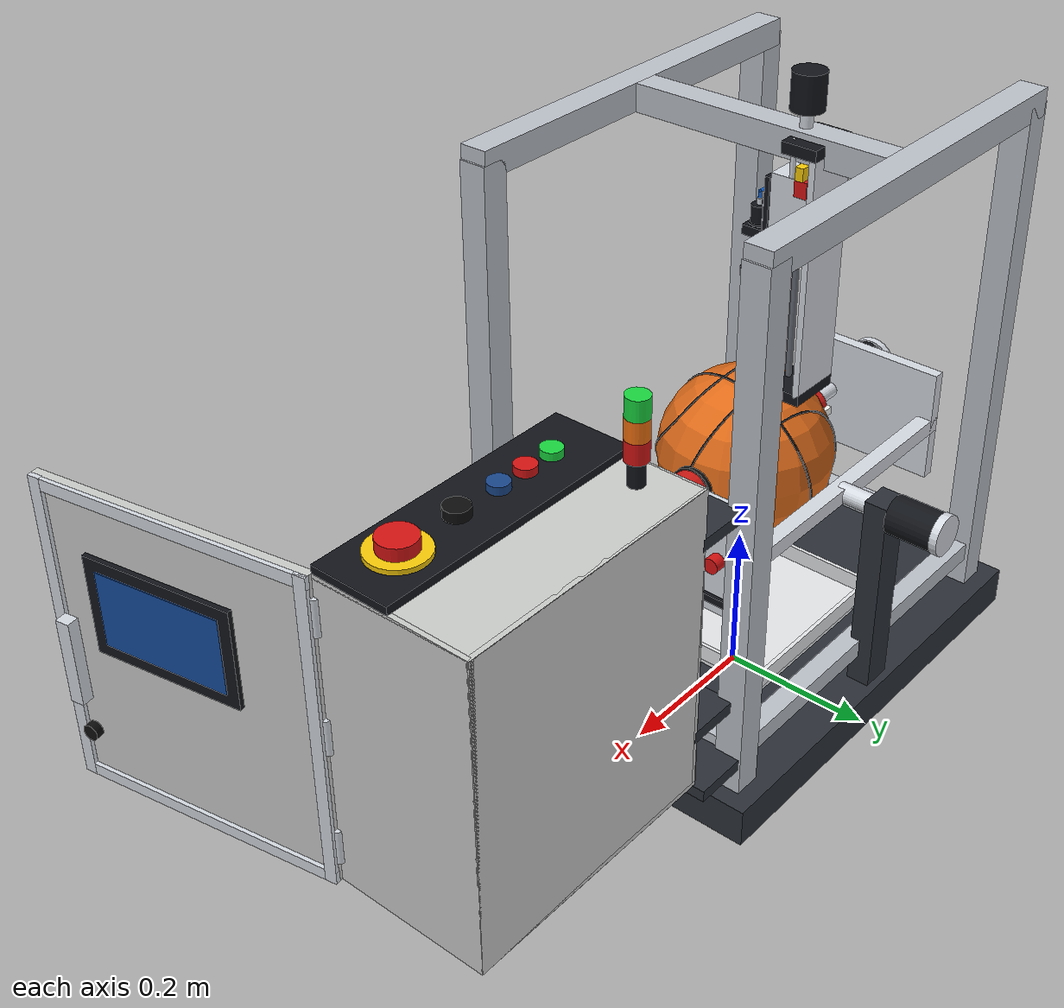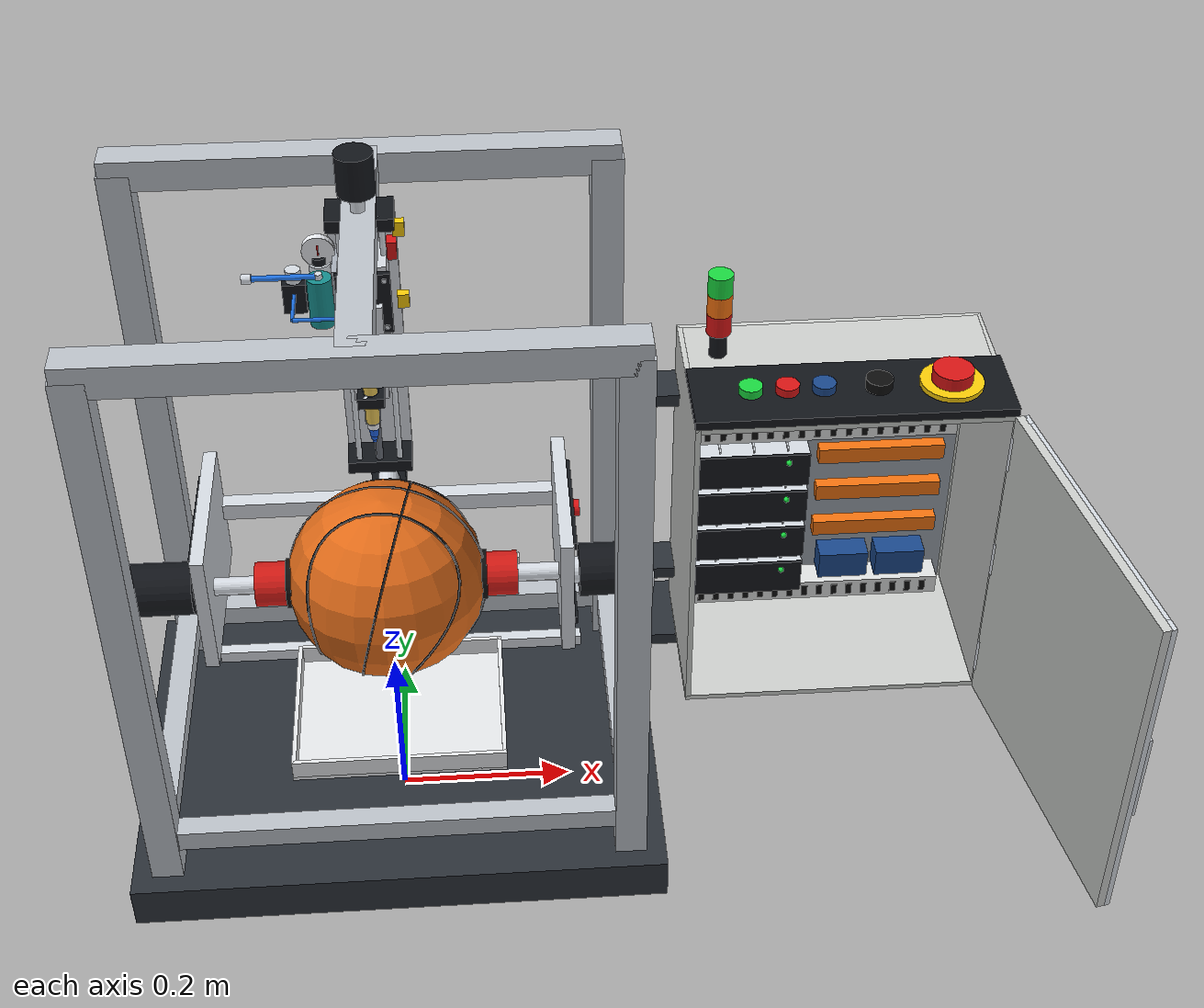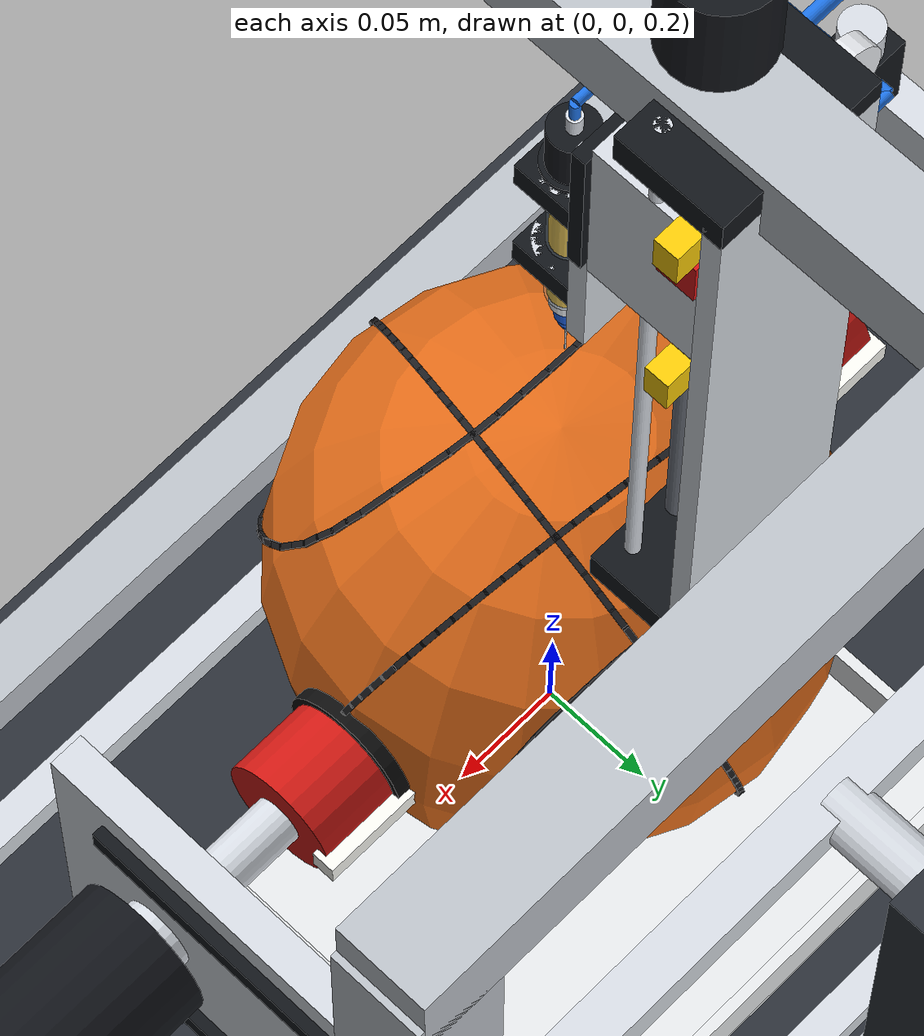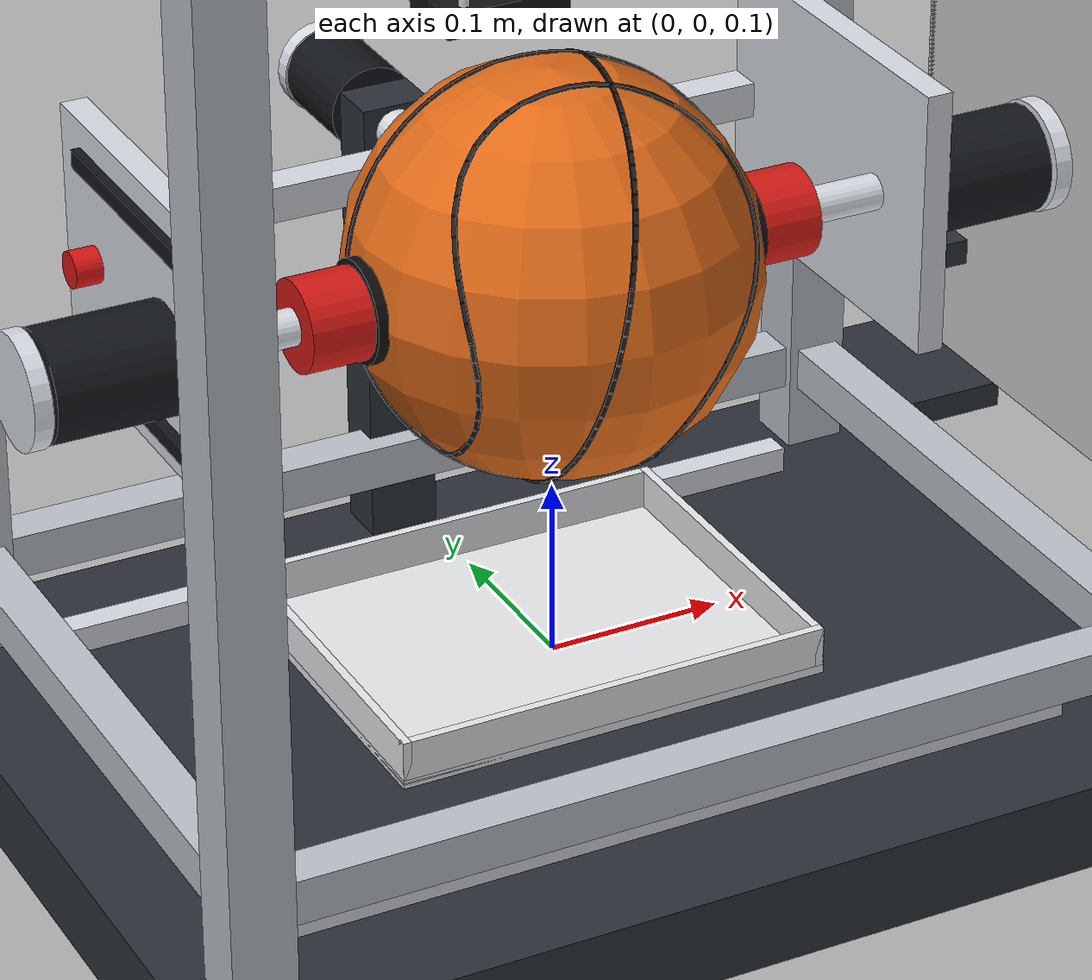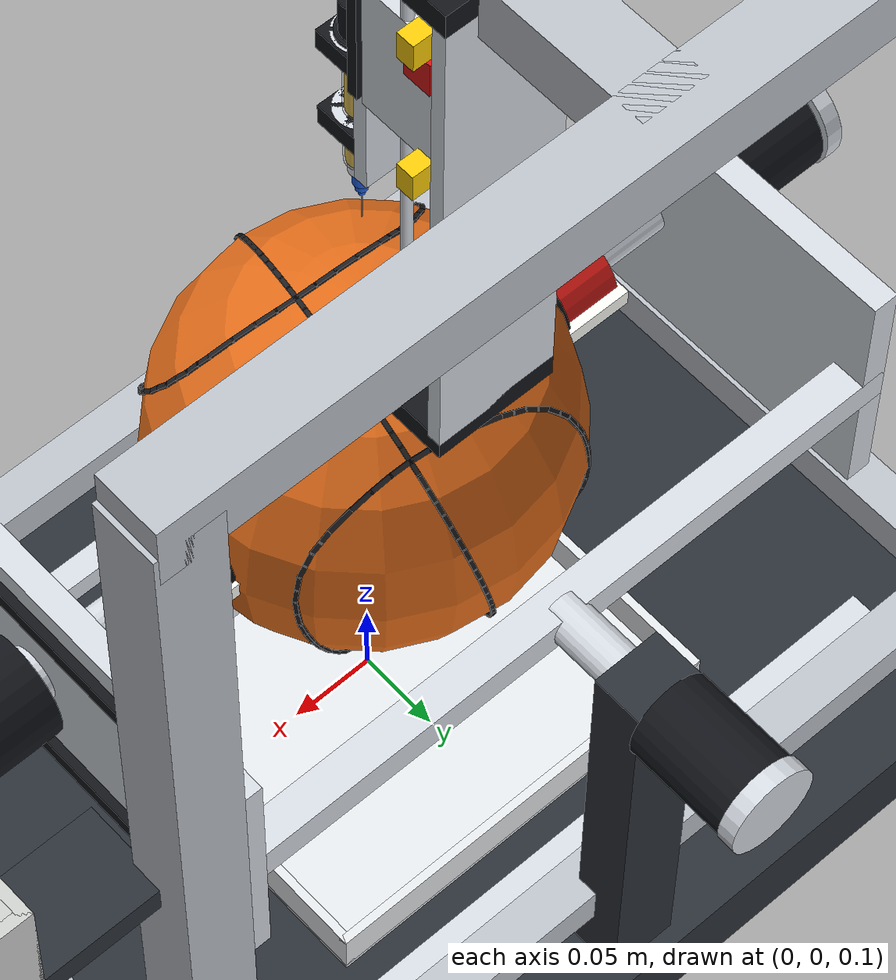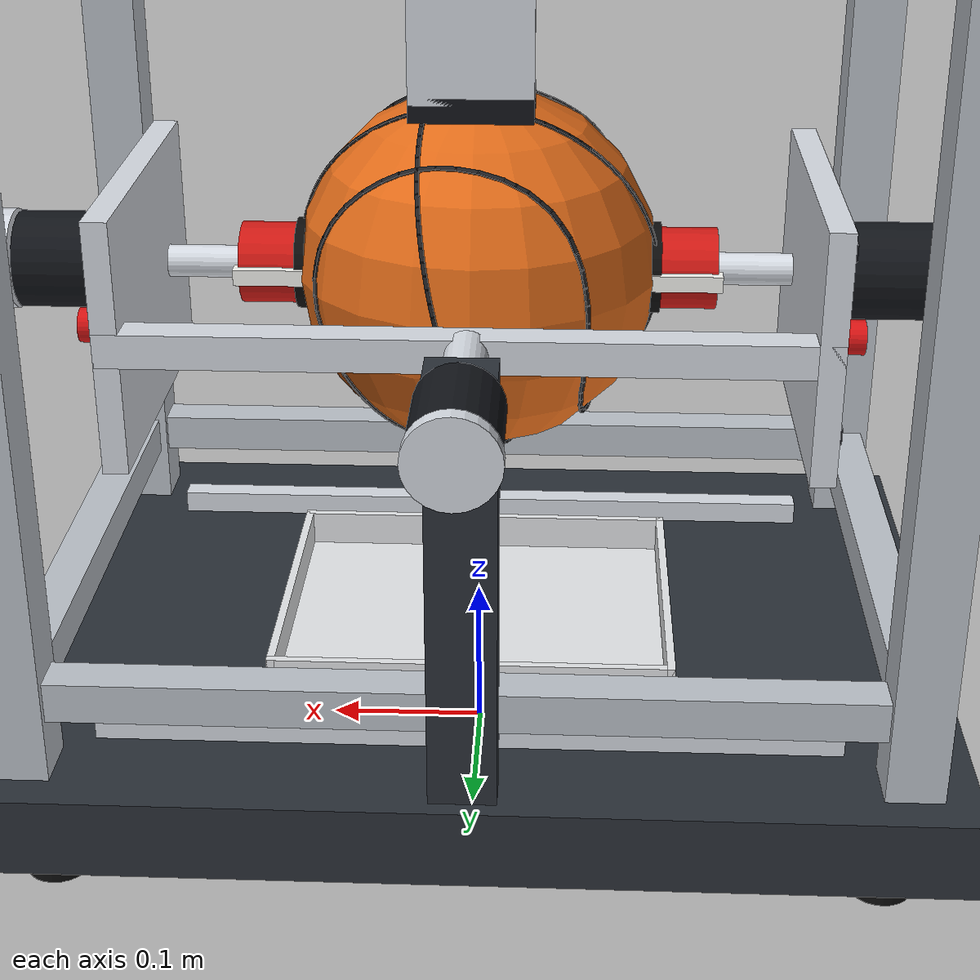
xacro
<?xml version="1.0"?>
<robot xmlns:xacro="http://www.ros.org/wiki/xacro" name="football_gumming_machine">
  <material name="frame_gray"><color rgba="0.17 0.19 0.22 1"/></material>
  <material name="alu_frame"><color rgba="0.74 0.76 0.79 1"/></material>
  <material name="rail_silver"><color rgba="0.84 0.86 0.89 1"/></material>
  <material name="alu_anodised"><color rgba="0.66 0.69 0.73 1"/></material>
  <material name="steel_dark"><color rgba="0.40 0.42 0.46 1"/></material>
  <material name="stainless"><color rgba="0.90 0.91 0.92 1"/></material>
  <material name="galvanised"><color rgba="0.60 0.63 0.67 1"/></material>
  <material name="rubber_black"><color rgba="0.05 0.05 0.05 1"/></material>
  <material name="motor_dark"><color rgba="0.07 0.08 0.10 1"/></material>
  <material name="cup_red"><color rgba="0.82 0.10 0.08 1"/></material>
  <material name="glue_amber"><color rgba="0.98 0.74 0.08 1"/></material>
  <material name="barrel_clear"><color rgba="0.80 0.90 0.97 0.30"/></material>
  <material name="tip_blue"><color rgba="0.12 0.38 0.88 1"/></material>
  <material name="luer_white"><color rgba="0.92 0.93 0.95 1"/></material>
  <material name="hose_blue"><color rgba="0.12 0.45 0.90 1"/></material>
  <material name="dryer_teal"><color rgba="0.08 0.55 0.55 1"/></material>
  <material name="football_white"><color rgba="0.97 0.97 0.95 1"/></material>
  <material name="patch_black"><color rgba="0.04 0.04 0.05 1"/></material>
  <material name="vb_yellow"><color rgba="0.97 0.80 0.10 1"/></material>
  <material name="vb_blue"><color rgba="0.10 0.30 0.70 1"/></material>
  <material name="bb_orange"><color rgba="0.88 0.42 0.10 1"/></material>
  <material name="seam_black"><color rgba="0.12 0.12 0.13 1"/></material>
  <material name="enclosure_grey"><color rgba="0.80 0.81 0.80 1"/></material>
  <material name="duct_grey"><color rgba="0.88 0.89 0.89 1"/></material>
  <material name="pcb_green"><color rgba="0.05 0.38 0.14 1"/></material>
  <material name="hmi_blue"><color rgba="0.08 0.30 0.62 1"/></material>
  <material name="cabinet_blue"><color rgba="0.10 0.28 0.55 1"/></material>
  <material name="safety_yellow"><color rgba="0.98 0.80 0.03 1"/></material>
  <material name="green_led"><color rgba="0.10 0.85 0.25 1"/></material>
  <material name="red_btn"><color rgba="0.85 0.08 0.08 1"/></material>
  <material name="nozzle_orange"><color rgba="0.96 0.45 0.06 1"/></material>
  <material name="nozzle_orange_old"><color rgba="0.95 0.35 0.06 1"/></material>

  <link name="world"/>
  <joint name="world_fixed" type="fixed">
    <parent link="world"/><child link="base_link"/><origin xyz="0 0 -0.07"/>
  </joint>

  <link name="base_link">
    <inertial><mass value="30.0"/><inertia ixx="3.0" ixy="0" ixz="0" iyy="3.0" iyz="0" izz="3.0"/></inertial>
    <visual><origin xyz="0 0 0.125"/><geometry><box size="0.6 0.45 0.05"/></geometry><material name="frame_gray"/></visual>
    <collision><origin xyz="0 0 0.125"/><geometry><box size="0.6 0.45 0.05"/></geometry></collision>
    <visual name="rail_a"><origin xyz="0 -0.15 0.1575" rpy="0 0 0"/><geometry><box size="0.45 0.015 0.015"/></geometry><material name="rail_silver"/></visual>
    <visual name="rail_b"><origin xyz="0 0.15 0.1575" rpy="0 0 0"/><geometry><box size="0.45 0.015 0.015"/></geometry><material name="rail_silver"/></visual>
    <visual name="cab_back"><origin xyz="0.515 0.182 0.4" rpy="0 0 0"/><geometry><box size="0.35 0.006 0.4"/></geometry><material name="enclosure_grey"/></visual>
    <visual name="cab_left"><origin xyz="0.343 0.085 0.4" rpy="0 0 0"/><geometry><box size="0.006 0.2 0.4"/></geometry><material name="enclosure_grey"/></visual>
    <visual name="cab_right"><origin xyz="0.687 0.085 0.4" rpy="0 0 0"/><geometry><box size="0.006 0.2 0.4"/></geometry><material name="enclosure_grey"/></visual>
    <visual name="cab_top"><origin xyz="0.515 0.085 0.597" rpy="0 0 0"/><geometry><box size="0.35 0.2 0.006"/></geometry><material name="enclosure_grey"/></visual>
    <visual name="cab_bottom"><origin xyz="0.515 0.085 0.203" rpy="0 0 0"/><geometry><box size="0.35 0.2 0.006"/></geometry><material name="enclosure_grey"/></visual>
    <visual name="cab_bracket_-0.26"><origin xyz="0.3085 0.16 0.27" rpy="0 0 0"/><geometry><box size="0.07 0.05 0.015"/></geometry><material name="frame_gray"/></visual>
    <visual name="cab_bracket_0.26"><origin xyz="0.3085 0.16 0.53" rpy="0 0 0"/><geometry><box size="0.07 0.05 0.015"/></geometry><material name="frame_gray"/></visual>
    <visual name="cab_shelf"><origin xyz="0.3085 0.15 0.1925" rpy="0 0 0"/><geometry><box size="0.07 0.1 0.015"/></geometry><material name="frame_gray"/></visual>
    <visual name="cab_backplate"><origin xyz="0.515 0.177 0.4" rpy="0 0 0"/><geometry><box size="0.33 0.004 0.38"/></geometry><material name="galvanised"/></visual>
    <visual name="din_rail_top"><origin xyz="0.515 0.173 0.495" rpy="0 0 0"/><geometry><box size="0.31 0.003 0.015"/></geometry><material name="duct_grey"/></visual>
    <visual name="din_rail_drive_0.06"><origin xyz="0.43 0.173 0.4075" rpy="0 0 0"/><geometry><box size="0.15 0.003 0.01"/></geometry><material name="duct_grey"/></visual>
    <visual name="din_rail_drive_-0.05"><origin xyz="0.43 0.173 0.3525" rpy="0 0 0"/><geometry><box size="0.15 0.003 0.01"/></geometry><material name="duct_grey"/></visual>
    <visual name="din_rail_drive_-0.16"><origin xyz="0.43 0.173 0.2975" rpy="0 0 0"/><geometry><box size="0.15 0.003 0.01"/></geometry><material name="duct_grey"/></visual>
    <visual name="din_rail_drive_-0.27"><origin xyz="0.43 0.173 0.2425" rpy="0 0 0"/><geometry><box size="0.15 0.003 0.01"/></geometry><material name="duct_grey"/></visual>
    <visual name="psu_smps"><origin xyz="0.42 0.149 0.525" rpy="0 0 0"/><geometry><box size="0.12 0.045 0.06"/></geometry><material name="rail_silver"/></visual>
    <visual name="psu_notch_top_0"><origin xyz="0.375 0.149 0.556" rpy="0 0 0"/><geometry><box size="0.01 0.025 0.005"/></geometry><material name="rubber_black"/></visual>
    <visual name="psu_notch_bot_0"><origin xyz="0.375 0.149 0.494" rpy="0 0 0"/><geometry><box size="0.01 0.025 0.005"/></geometry><material name="rubber_black"/></visual>
    <visual name="psu_notch_top_1"><origin xyz="0.393 0.149 0.556" rpy="0 0 0"/><geometry><box size="0.01 0.025 0.005"/></geometry><material name="rubber_black"/></visual>
    <visual name="psu_notch_bot_1"><origin xyz="0.393 0.149 0.494" rpy="0 0 0"/><geometry><box size="0.01 0.025 0.005"/></geometry><material name="rubber_black"/></visual>
    <visual name="psu_notch_top_2"><origin xyz="0.411 0.149 0.556" rpy="0 0 0"/><geometry><box size="0.01 0.025 0.005"/></geometry><material name="rubber_black"/></visual>
    <visual name="psu_notch_bot_2"><origin xyz="0.411 0.149 0.494" rpy="0 0 0"/><geometry><box size="0.01 0.025 0.005"/></geometry><material name="rubber_black"/></visual>
    <visual name="psu_notch_top_3"><origin xyz="0.429 0.149 0.556" rpy="0 0 0"/><geometry><box size="0.01 0.025 0.005"/></geometry><material name="rubber_black"/></visual>
    <visual name="psu_notch_bot_3"><origin xyz="0.429 0.149 0.494" rpy="0 0 0"/><geometry><box size="0.01 0.025 0.005"/></geometry><material name="rubber_black"/></visual>
    <visual name="psu_notch_top_4"><origin xyz="0.447 0.149 0.556" rpy="0 0 0"/><geometry><box size="0.01 0.025 0.005"/></geometry><material name="rubber_black"/></visual>
    <visual name="psu_notch_bot_4"><origin xyz="0.447 0.149 0.494" rpy="0 0 0"/><geometry><box size="0.01 0.025 0.005"/></geometry><material name="rubber_black"/></visual>
    <visual name="psu_notch_top_5"><origin xyz="0.465 0.149 0.556" rpy="0 0 0"/><geometry><box size="0.01 0.025 0.005"/></geometry><material name="rubber_black"/></visual>
    <visual name="psu_notch_bot_5"><origin xyz="0.465 0.149 0.494" rpy="0 0 0"/><geometry><box size="0.01 0.025 0.005"/></geometry><material name="rubber_black"/></visual>
    <visual name="psu_label"><origin xyz="0.42 0.126 0.525" rpy="0 0 0"/><geometry><box size="0.07 0.002 0.025"/></geometry><material name="nozzle_orange"/></visual>
    <visual name="plc_module"><origin xyz="0.58 0.149 0.525" rpy="0 0 0"/><geometry><box size="0.18 0.04 0.06"/></geometry><material name="motor_dark"/></visual>
    <visual name="plc_cpu"><origin xyz="0.53 0.128 0.525" rpy="0 0 0"/><geometry><box size="0.05 0.002 0.045"/></geometry><material name="pcb_green"/></visual>
    <visual name="plc_led_0"><origin xyz="0.56 0.128 0.54"/><geometry><sphere radius="0.003"/></geometry><material name="nozzle_orange"/></visual>
    <visual name="plc_led_1"><origin xyz="0.5717 0.128 0.54"/><geometry><sphere radius="0.003"/></geometry><material name="green_led"/></visual>
    <visual name="plc_led_2"><origin xyz="0.5834 0.128 0.54"/><geometry><sphere radius="0.003"/></geometry><material name="green_led"/></visual>
    <visual name="plc_led_3"><origin xyz="0.5951 0.128 0.54"/><geometry><sphere radius="0.003"/></geometry><material name="nozzle_orange"/></visual>
    <visual name="plc_led_4"><origin xyz="0.6068 0.128 0.54"/><geometry><sphere radius="0.003"/></geometry><material name="green_led"/></visual>
    <visual name="plc_led_5"><origin xyz="0.6185 0.128 0.54"/><geometry><sphere radius="0.003"/></geometry><material name="green_led"/></visual>
    <visual name="plc_led_6"><origin xyz="0.6302 0.128 0.54"/><geometry><sphere radius="0.003"/></geometry><material name="nozzle_orange"/></visual>
    <visual name="plc_led_7"><origin xyz="0.6419 0.128 0.54"/><geometry><sphere radius="0.003"/></geometry><material name="green_led"/></visual>
    <visual name="plc_led_8"><origin xyz="0.6536 0.128 0.54"/><geometry><sphere radius="0.003"/></geometry><material name="green_led"/></visual>
    <visual name="plc_led_9"><origin xyz="0.6653 0.128 0.54"/><geometry><sphere radius="0.003"/></geometry><material name="nozzle_orange"/></visual>
    <visual name="duct_top"><origin xyz="0.515 0.159 0.575" rpy="0 0 0"/><geometry><box size="0.31 0.035 0.025"/></geometry><material name="duct_grey"/></visual>
    <visual name="duct_top_slot_0"><origin xyz="0.375 0.14175 0.575" rpy="0 0 0"/><geometry><box size="0.007 0.002 0.015"/></geometry><material name="rubber_black"/></visual>
    <visual name="duct_top_slot_1"><origin xyz="0.3935 0.14175 0.575" rpy="0 0 0"/><geometry><box size="0.007 0.002 0.015"/></geometry><material name="rubber_black"/></visual>
    <visual name="duct_top_slot_2"><origin xyz="0.412 0.14175 0.575" rpy="0 0 0"/><geometry><box size="0.007 0.002 0.015"/></geometry><material name="rubber_black"/></visual>
    <visual name="duct_top_slot_3"><origin xyz="0.4305 0.14175 0.575" rpy="0 0 0"/><geometry><box size="0.007 0.002 0.015"/></geometry><material name="rubber_black"/></visual>
    <visual name="duct_top_slot_4"><origin xyz="0.449 0.14175 0.575" rpy="0 0 0"/><geometry><box size="0.007 0.002 0.015"/></geometry><material name="rubber_black"/></visual>
    <visual name="duct_top_slot_5"><origin xyz="0.4675 0.14175 0.575" rpy="0 0 0"/><geometry><box size="0.007 0.002 0.015"/></geometry><material name="rubber_black"/></visual>
    <visual name="duct_top_slot_6"><origin xyz="0.486 0.14175 0.575" rpy="0 0 0"/><geometry><box size="0.007 0.002 0.015"/></geometry><material name="rubber_black"/></visual>
    <visual name="duct_top_slot_7"><origin xyz="0.5045 0.14175 0.575" rpy="0 0 0"/><geometry><box size="0.007 0.002 0.015"/></geometry><material name="rubber_black"/></visual>
    <visual name="duct_top_slot_8"><origin xyz="0.523 0.14175 0.575" rpy="0 0 0"/><geometry><box size="0.007 0.002 0.015"/></geometry><material name="rubber_black"/></visual>
    <visual name="duct_top_slot_9"><origin xyz="0.5415 0.14175 0.575" rpy="0 0 0"/><geometry><box size="0.007 0.002 0.015"/></geometry><material name="rubber_black"/></visual>
    <visual name="duct_top_slot_10"><origin xyz="0.56 0.14175 0.575" rpy="0 0 0"/><geometry><box size="0.007 0.002 0.015"/></geometry><material name="rubber_black"/></visual>
    <visual name="duct_top_slot_11"><origin xyz="0.5785 0.14175 0.575" rpy="0 0 0"/><geometry><box size="0.007 0.002 0.015"/></geometry><material name="rubber_black"/></visual>
    <visual name="duct_top_slot_12"><origin xyz="0.597 0.14175 0.575" rpy="0 0 0"/><geometry><box size="0.007 0.002 0.015"/></geometry><material name="rubber_black"/></visual>
    <visual name="duct_top_slot_13"><origin xyz="0.6155 0.14175 0.575" rpy="0 0 0"/><geometry><box size="0.007 0.002 0.015"/></geometry><material name="rubber_black"/></visual>
    <visual name="duct_top_slot_14"><origin xyz="0.634 0.14175 0.575" rpy="0 0 0"/><geometry><box size="0.007 0.002 0.015"/></geometry><material name="rubber_black"/></visual>
    <visual name="duct_top_slot_15"><origin xyz="0.6525 0.14175 0.575" rpy="0 0 0"/><geometry><box size="0.007 0.002 0.015"/></geometry><material name="rubber_black"/></visual>
    <visual name="duct_mid"><origin xyz="0.515 0.159 0.4725" rpy="0 0 0"/><geometry><box size="0.31 0.035 0.025"/></geometry><material name="duct_grey"/></visual>
    <visual name="duct_mid_slot_0"><origin xyz="0.375 0.14175 0.4725" rpy="0 0 0"/><geometry><box size="0.007 0.002 0.015"/></geometry><material name="rubber_black"/></visual>
    <visual name="duct_mid_slot_1"><origin xyz="0.3935 0.14175 0.4725" rpy="0 0 0"/><geometry><box size="0.007 0.002 0.015"/></geometry><material name="rubber_black"/></visual>
    <visual name="duct_mid_slot_2"><origin xyz="0.412 0.14175 0.4725" rpy="0 0 0"/><geometry><box size="0.007 0.002 0.015"/></geometry><material name="rubber_black"/></visual>
    <visual name="duct_mid_slot_3"><origin xyz="0.4305 0.14175 0.4725" rpy="0 0 0"/><geometry><box size="0.007 0.002 0.015"/></geometry><material name="rubber_black"/></visual>
    <visual name="duct_mid_slot_4"><origin xyz="0.449 0.14175 0.4725" rpy="0 0 0"/><geometry><box size="0.007 0.002 0.015"/></geometry><material name="rubber_black"/></visual>
    <visual name="duct_mid_slot_5"><origin xyz="0.4675 0.14175 0.4725" rpy="0 0 0"/><geometry><box size="0.007 0.002 0.015"/></geometry><material name="rubber_black"/></visual>
    <visual name="duct_mid_slot_6"><origin xyz="0.486 0.14175 0.4725" rpy="0 0 0"/><geometry><box size="0.007 0.002 0.015"/></geometry><material name="rubber_black"/></visual>
    <visual name="duct_mid_slot_7"><origin xyz="0.5045 0.14175 0.4725" rpy="0 0 0"/><geometry><box size="0.007 0.002 0.015"/></geometry><material name="rubber_black"/></visual>
    <visual name="duct_mid_slot_8"><origin xyz="0.523 0.14175 0.4725" rpy="0 0 0"/><geometry><box size="0.007 0.002 0.015"/></geometry><material name="rubber_black"/></visual>
    <visual name="duct_mid_slot_9"><origin xyz="0.5415 0.14175 0.4725" rpy="0 0 0"/><geometry><box size="0.007 0.002 0.015"/></geometry><material name="rubber_black"/></visual>
    <visual name="duct_mid_slot_10"><origin xyz="0.56 0.14175 0.4725" rpy="0 0 0"/><geometry><box size="0.007 0.002 0.015"/></geometry><material name="rubber_black"/></visual>
    <visual name="duct_mid_slot_11"><origin xyz="0.5785 0.14175 0.4725" rpy="0 0 0"/><geometry><box size="0.007 0.002 0.015"/></geometry><material name="rubber_black"/></visual>
    <visual name="duct_mid_slot_12"><origin xyz="0.597 0.14175 0.4725" rpy="0 0 0"/><geometry><box size="0.007 0.002 0.015"/></geometry><material name="rubber_black"/></visual>
    <visual name="duct_mid_slot_13"><origin xyz="0.6155 0.14175 0.4725" rpy="0 0 0"/><geometry><box size="0.007 0.002 0.015"/></geometry><material name="rubber_black"/></visual>
    <visual name="duct_mid_slot_14"><origin xyz="0.634 0.14175 0.4725" rpy="0 0 0"/><geometry><box size="0.007 0.002 0.015"/></geometry><material name="rubber_black"/></visual>
    <visual name="duct_mid_slot_15"><origin xyz="0.6525 0.14175 0.4725" rpy="0 0 0"/><geometry><box size="0.007 0.002 0.015"/></geometry><material name="rubber_black"/></visual>
    <visual name="duct_bottom"><origin xyz="0.515 0.159 0.225" rpy="0 0 0"/><geometry><box size="0.31 0.035 0.025"/></geometry><material name="duct_grey"/></visual>
    <visual name="duct_bottom_slot_0"><origin xyz="0.375 0.14175 0.225" rpy="0 0 0"/><geometry><box size="0.007 0.002 0.015"/></geometry><material name="rubber_black"/></visual>
    <visual name="duct_bottom_slot_1"><origin xyz="0.3935 0.14175 0.225" rpy="0 0 0"/><geometry><box size="0.007 0.002 0.015"/></geometry><material name="rubber_black"/></visual>
    <visual name="duct_bottom_slot_2"><origin xyz="0.412 0.14175 0.225" rpy="0 0 0"/><geometry><box size="0.007 0.002 0.015"/></geometry><material name="rubber_black"/></visual>
    <visual name="duct_bottom_slot_3"><origin xyz="0.4305 0.14175 0.225" rpy="0 0 0"/><geometry><box size="0.007 0.002 0.015"/></geometry><material name="rubber_black"/></visual>
    <visual name="duct_bottom_slot_4"><origin xyz="0.449 0.14175 0.225" rpy="0 0 0"/><geometry><box size="0.007 0.002 0.015"/></geometry><material name="rubber_black"/></visual>
    <visual name="duct_bottom_slot_5"><origin xyz="0.4675 0.14175 0.225" rpy="0 0 0"/><geometry><box size="0.007 0.002 0.015"/></geometry><material name="rubber_black"/></visual>
    <visual name="duct_bottom_slot_6"><origin xyz="0.486 0.14175 0.225" rpy="0 0 0"/><geometry><box size="0.007 0.002 0.015"/></geometry><material name="rubber_black"/></visual>
    <visual name="duct_bottom_slot_7"><origin xyz="0.5045 0.14175 0.225" rpy="0 0 0"/><geometry><box size="0.007 0.002 0.015"/></geometry><material name="rubber_black"/></visual>
    <visual name="duct_bottom_slot_8"><origin xyz="0.523 0.14175 0.225" rpy="0 0 0"/><geometry><box size="0.007 0.002 0.015"/></geometry><material name="rubber_black"/></visual>
    <visual name="duct_bottom_slot_9"><origin xyz="0.5415 0.14175 0.225" rpy="0 0 0"/><geometry><box size="0.007 0.002 0.015"/></geometry><material name="rubber_black"/></visual>
    <visual name="duct_bottom_slot_10"><origin xyz="0.56 0.14175 0.225" rpy="0 0 0"/><geometry><box size="0.007 0.002 0.015"/></geometry><material name="rubber_black"/></visual>
    <visual name="duct_bottom_slot_11"><origin xyz="0.5785 0.14175 0.225" rpy="0 0 0"/><geometry><box size="0.007 0.002 0.015"/></geometry><material name="rubber_black"/></visual>
    <visual name="duct_bottom_slot_12"><origin xyz="0.597 0.14175 0.225" rpy="0 0 0"/><geometry><box size="0.007 0.002 0.015"/></geometry><material name="rubber_black"/></visual>
    <visual name="duct_bottom_slot_13"><origin xyz="0.6155 0.14175 0.225" rpy="0 0 0"/><geometry><box size="0.007 0.002 0.015"/></geometry><material name="rubber_black"/></visual>
    <visual name="duct_bottom_slot_14"><origin xyz="0.634 0.14175 0.225" rpy="0 0 0"/><geometry><box size="0.007 0.002 0.015"/></geometry><material name="rubber_black"/></visual>
    <visual name="duct_bottom_slot_15"><origin xyz="0.6525 0.14175 0.225" rpy="0 0 0"/><geometry><box size="0.007 0.002 0.015"/></geometry><material name="rubber_black"/></visual>
    <visual name="drive_0_body"><origin xyz="0.43 0.149 0.43" rpy="0 0 0"/><geometry><box size="0.13 0.045 0.045"/></geometry><material name="rail_silver"/></visual>
    <visual name="drive_0_fin_-0.08"><origin xyz="0.39 0.149 0.4535" rpy="0 0 0"/><geometry><box size="0.002 0.035 0.003"/></geometry><material name="rail_silver"/></visual>
    <visual name="drive_0_fin_0.0"><origin xyz="0.43 0.149 0.4535" rpy="0 0 0"/><geometry><box size="0.002 0.035 0.003"/></geometry><material name="rail_silver"/></visual>
    <visual name="drive_0_fin_0.08"><origin xyz="0.47 0.149 0.4535" rpy="0 0 0"/><geometry><box size="0.002 0.035 0.003"/></geometry><material name="rail_silver"/></visual>
    <visual name="drive_0_front"><origin xyz="0.43 0.125 0.43" rpy="0 0 0"/><geometry><box size="0.13 0.003 0.045"/></geometry><material name="motor_dark"/></visual>
    <visual name="drive_0_led"><origin xyz="0.47 0.122 0.4425"/><geometry><sphere radius="0.0035"/></geometry><material name="green_led"/></visual>
    <visual name="drive_1_body"><origin xyz="0.43 0.149 0.375" rpy="0 0 0"/><geometry><box size="0.13 0.045 0.045"/></geometry><material name="rail_silver"/></visual>
    <visual name="drive_1_fin_-0.08"><origin xyz="0.39 0.149 0.3985" rpy="0 0 0"/><geometry><box size="0.002 0.035 0.003"/></geometry><material name="rail_silver"/></visual>
    <visual name="drive_1_fin_0.0"><origin xyz="0.43 0.149 0.3985" rpy="0 0 0"/><geometry><box size="0.002 0.035 0.003"/></geometry><material name="rail_silver"/></visual>
    <visual name="drive_1_fin_0.08"><origin xyz="0.47 0.149 0.3985" rpy="0 0 0"/><geometry><box size="0.002 0.035 0.003"/></geometry><material name="rail_silver"/></visual>
    <visual name="drive_1_front"><origin xyz="0.43 0.125 0.375" rpy="0 0 0"/><geometry><box size="0.13 0.003 0.045"/></geometry><material name="motor_dark"/></visual>
    <visual name="drive_1_led"><origin xyz="0.47 0.122 0.3875"/><geometry><sphere radius="0.0035"/></geometry><material name="green_led"/></visual>
    <visual name="drive_2_body"><origin xyz="0.43 0.149 0.32" rpy="0 0 0"/><geometry><box size="0.13 0.045 0.045"/></geometry><material name="rail_silver"/></visual>
    <visual name="drive_2_fin_-0.08"><origin xyz="0.39 0.149 0.3435" rpy="0 0 0"/><geometry><box size="0.002 0.035 0.003"/></geometry><material name="rail_silver"/></visual>
    <visual name="drive_2_fin_0.0"><origin xyz="0.43 0.149 0.3435" rpy="0 0 0"/><geometry><box size="0.002 0.035 0.003"/></geometry><material name="rail_silver"/></visual>
    <visual name="drive_2_fin_0.08"><origin xyz="0.47 0.149 0.3435" rpy="0 0 0"/><geometry><box size="0.002 0.035 0.003"/></geometry><material name="rail_silver"/></visual>
    <visual name="drive_2_front"><origin xyz="0.43 0.125 0.32" rpy="0 0 0"/><geometry><box size="0.13 0.003 0.045"/></geometry><material name="motor_dark"/></visual>
    <visual name="drive_2_led"><origin xyz="0.47 0.122 0.3325"/><geometry><sphere radius="0.0035"/></geometry><material name="green_led"/></visual>
    <visual name="drive_3_body"><origin xyz="0.43 0.149 0.265" rpy="0 0 0"/><geometry><box size="0.13 0.045 0.045"/></geometry><material name="rail_silver"/></visual>
    <visual name="drive_3_fin_-0.08"><origin xyz="0.39 0.149 0.2885" rpy="0 0 0"/><geometry><box size="0.002 0.035 0.003"/></geometry><material name="rail_silver"/></visual>
    <visual name="drive_3_fin_0.0"><origin xyz="0.43 0.149 0.2885" rpy="0 0 0"/><geometry><box size="0.002 0.035 0.003"/></geometry><material name="rail_silver"/></visual>
    <visual name="drive_3_fin_0.08"><origin xyz="0.47 0.149 0.2885" rpy="0 0 0"/><geometry><box size="0.002 0.035 0.003"/></geometry><material name="rail_silver"/></visual>
    <visual name="drive_3_front"><origin xyz="0.43 0.125 0.265" rpy="0 0 0"/><geometry><box size="0.13 0.003 0.045"/></geometry><material name="motor_dark"/></visual>
    <visual name="drive_3_led"><origin xyz="0.47 0.122 0.2775"/><geometry><sphere radius="0.0035"/></geometry><material name="green_led"/></visual>
    <visual name="terminal_strip_0.06"><origin xyz="0.585 0.154 0.43" rpy="0 0 0"/><geometry><box size="0.15 0.015 0.02"/></geometry><material name="nozzle_orange"/></visual>
    <visual name="terminal_strip_-0.05"><origin xyz="0.585 0.154 0.375" rpy="0 0 0"/><geometry><box size="0.15 0.015 0.02"/></geometry><material name="nozzle_orange"/></visual>
    <visual name="terminal_strip_-0.16"><origin xyz="0.585 0.154 0.32" rpy="0 0 0"/><geometry><box size="0.15 0.015 0.02"/></geometry><material name="nozzle_orange"/></visual>
    <visual name="relay_0"><origin xyz="0.55 0.154 0.265" rpy="0 0 0"/><geometry><box size="0.06 0.03 0.035"/></geometry><material name="cabinet_blue"/></visual>
    <visual name="relay_1"><origin xyz="0.62 0.154 0.265" rpy="0 0 0"/><geometry><box size="0.06 0.03 0.035"/></geometry><material name="cabinet_blue"/></visual>
    <visual name="cab_door"><origin xyz="0.72039 -0.18734 0.4" rpy="0 0 1.74533"/><geometry><box size="0.35 0.01 0.4"/></geometry><material name="enclosure_grey"/></visual>
    <visual name="door_bezel_top"><origin xyz="0.72728 -0.186125 0.5925" rpy="0 0 1.74533"/><geometry><box size="0.35 0.006 0.015"/></geometry><material name="rail_silver"/></visual>
    <visual name="door_bezel_bottom"><origin xyz="0.72728 -0.186125 0.2075" rpy="0 0 1.74533"/><geometry><box size="0.35 0.006 0.015"/></geometry><material name="rail_silver"/></visual>
    <visual name="door_bezel_left"><origin xyz="0.75637 -0.35108 0.4" rpy="0 0 1.74533"/><geometry><box size="0.015 0.006 0.4"/></geometry><material name="rail_silver"/></visual>
    <visual name="door_bezel_right"><origin xyz="0.698195 -0.02117 0.4" rpy="0 0 1.74533"/><geometry><box size="0.015 0.006 0.4"/></geometry><material name="rail_silver"/></visual>
    <visual name="hmi_frame"><origin xyz="0.733215 -0.20539 0.46" rpy="0 0 1.74533"/><geometry><box size="0.19 0.006 0.125"/></geometry><material name="motor_dark"/></visual>
    <visual name="hmi_screen_7in"><origin xyz="0.73642 -0.204825 0.46" rpy="0 0 1.74533"/><geometry><box size="0.16 0.002 0.095"/></geometry><material name="hmi_blue"/></visual>
    <visual name="door_handle"><origin xyz="0.76367 -0.332025 0.375" rpy="0 0 1.74533"/><geometry><box size="0.0175 0.015 0.11"/></geometry><material name="rail_silver"/></visual>
    <visual name="door_latch"><origin xyz="0.75727 -0.333155 0.27" rpy="1.5708 0 1.74533"/><geometry><cylinder radius="0.01" length="0.01"/></geometry><material name="rubber_black"/></visual>
    <visual name="door_hinge_0.3"><origin xyz="0.69 -0.015 0.55" rpy="0 0 0"/><geometry><cylinder radius="0.006" length="0.045"/></geometry><material name="rail_silver"/></visual>
    <visual name="door_hinge_0.0"><origin xyz="0.69 -0.015 0.4" rpy="0 0 0"/><geometry><cylinder radius="0.006" length="0.045"/></geometry><material name="rail_silver"/></visual>
    <visual name="door_hinge_-0.3"><origin xyz="0.69 -0.015 0.25" rpy="0 0 0"/><geometry><cylinder radius="0.006" length="0.045"/></geometry><material name="rail_silver"/></visual>
    <visual name="ctrl_deck"><origin xyz="0.515 0.035 0.605" rpy="0 0 0"/><geometry><box size="0.35 0.1 0.01"/></geometry><material name="motor_dark"/></visual>
    <visual name="estop_yellow_ring"><origin xyz="0.625 0.035 0.613" rpy="0 0 0"/><geometry><cylinder radius="0.035" length="0.006"/></geometry><material name="safety_yellow"/></visual>
    <visual name="estop_button"><origin xyz="0.625 0.035 0.6235" rpy="0 0 0"/><geometry><cylinder radius="0.0225" length="0.015"/></geometry><material name="red_btn"/></visual>
    <visual name="btn_start"><origin xyz="0.405 0.035 0.615" rpy="0 0 0"/><geometry><cylinder radius="0.013" length="0.01"/></geometry><material name="green_led"/></visual>
    <visual name="btn_stop"><origin xyz="0.445 0.035 0.615" rpy="0 0 0"/><geometry><cylinder radius="0.013" length="0.01"/></geometry><material name="red_btn"/></visual>
    <visual name="btn_reset"><origin xyz="0.485 0.035 0.615" rpy="0 0 0"/><geometry><cylinder radius="0.013" length="0.01"/></geometry><material name="cabinet_blue"/></visual>
    <visual name="key_switch"><origin xyz="0.545 0.035 0.61625" rpy="0 0 0"/><geometry><cylinder radius="0.015" length="0.0125"/></geometry><material name="rubber_black"/></visual>
    <visual name="beacon_base"><origin xyz="0.38 0.125 0.615" rpy="0 0 0"/><geometry><cylinder radius="0.01" length="0.03"/></geometry><material name="motor_dark"/></visual>
    <visual name="beacon_light_0"><origin xyz="0.38 0.125 0.6425" rpy="0 0 0"/><geometry><cylinder radius="0.014" length="0.025"/></geometry><material name="red_btn"/></visual>
    <visual name="beacon_light_1"><origin xyz="0.38 0.125 0.6675" rpy="0 0 0"/><geometry><cylinder radius="0.014" length="0.025"/></geometry><material name="nozzle_orange"/></visual>
    <visual name="beacon_light_2"><origin xyz="0.38 0.125 0.6925" rpy="0 0 0"/><geometry><cylinder radius="0.014" length="0.025"/></geometry><material name="green_led"/></visual>
    <visual name="drip_tray_floor"><origin xyz="0 0.025 0.1625" rpy="0 0 0"/><geometry><box size="0.25 0.2 0.005"/></geometry><material name="stainless"/></visual>
    <visual name="drip_tray_front"><origin xyz="0 -0.0725 0.175" rpy="0 0 0"/><geometry><box size="0.25 0.005 0.025"/></geometry><material name="stainless"/></visual>
    <visual name="drip_tray_back"><origin xyz="0 0.1225 0.175" rpy="0 0 0"/><geometry><box size="0.25 0.005 0.025"/></geometry><material name="stainless"/></visual>
    <visual name="drip_tray_left"><origin xyz="-0.1225 0.025 0.175" rpy="0 0 0"/><geometry><box size="0.005 0.2 0.025"/></geometry><material name="stainless"/></visual>
    <visual name="drip_tray_right"><origin xyz="0.1225 0.025 0.175" rpy="0 0 0"/><geometry><box size="0.005 0.2 0.025"/></geometry><material name="stainless"/></visual>
    <visual name="foot_-0.5_-0.35"><origin xyz="-0.25 -0.175 0.085" rpy="0 0 0"/><geometry><cylinder radius="0.02" length="0.03"/></geometry><material name="rubber_black"/></visual>
    <visual name="foot_-0.5_0.35"><origin xyz="-0.25 0.175 0.085" rpy="0 0 0"/><geometry><cylinder radius="0.02" length="0.03"/></geometry><material name="rubber_black"/></visual>
    <visual name="foot_0.5_-0.35"><origin xyz="0.25 -0.175 0.085" rpy="0 0 0"/><geometry><cylinder radius="0.02" length="0.03"/></geometry><material name="rubber_black"/></visual>
    <visual name="foot_0.5_0.35"><origin xyz="0.25 0.175 0.085" rpy="0 0 0"/><geometry><cylinder radius="0.02" length="0.03"/></geometry><material name="rubber_black"/></visual>
  </link>
  <link name="left_front_post">
    <inertial><mass value="3.0"/><inertia ixx="0.491225" ixy="0" ixz="0" iyy="0.491225" iyz="0" izz="0.002450"/></inertial>
    <visual><geometry><box size="0.035 0.035 0.7"/></geometry><material name="alu_frame"/></visual>
    <collision><geometry><box size="0.035 0.035 0.7"/></geometry></collision>
  </link>
  <joint name="left_front_post_mount" type="fixed">
    <parent link="base_link"/><child link="left_front_post"/><origin xyz="-0.26 -0.185 0.475"/>
  </joint>
  <link name="left_back_post">
    <inertial><mass value="3.0"/><inertia ixx="0.491225" ixy="0" ixz="0" iyy="0.491225" iyz="0" izz="0.002450"/></inertial>
    <visual><geometry><box size="0.035 0.035 0.7"/></geometry><material name="alu_frame"/></visual>
    <collision><geometry><box size="0.035 0.035 0.7"/></geometry></collision>
  </link>
  <joint name="left_back_post_mount" type="fixed">
    <parent link="base_link"/><child link="left_back_post"/><origin xyz="-0.26 0.185 0.475"/>
  </joint>
  <link name="right_front_post">
    <inertial><mass value="3.0"/><inertia ixx="0.491225" ixy="0" ixz="0" iyy="0.491225" iyz="0" izz="0.002450"/></inertial>
    <visual><geometry><box size="0.035 0.035 0.7"/></geometry><material name="alu_frame"/></visual>
    <collision><geometry><box size="0.035 0.035 0.7"/></geometry></collision>
  </link>
  <joint name="right_front_post_mount" type="fixed">
    <parent link="base_link"/><child link="right_front_post"/><origin xyz="0.26 -0.185 0.475"/>
  </joint>
  <link name="right_back_post">
    <inertial><mass value="3.0"/><inertia ixx="0.491225" ixy="0" ixz="0" iyy="0.491225" iyz="0" izz="0.002450"/></inertial>
    <visual><geometry><box size="0.035 0.035 0.7"/></geometry><material name="alu_frame"/></visual>
    <collision><geometry><box size="0.035 0.035 0.7"/></geometry></collision>
  </link>
  <joint name="right_back_post_mount" type="fixed">
    <parent link="base_link"/><child link="right_back_post"/><origin xyz="0.26 0.185 0.475"/>
  </joint>
  <link name="top_front_beam">
    <inertial><mass value="3.0"/><inertia ixx="0.002450" ixy="0" ixz="0" iyy="0.303725" iyz="0" izz="0.303725"/></inertial>
    <visual><geometry><box size="0.55 0.035 0.035"/></geometry><material name="alu_frame"/></visual>
    <collision><geometry><box size="0.55 0.035 0.035"/></geometry></collision>
  </link>
  <joint name="front_beam_mount" type="fixed">
    <parent link="base_link"/><child link="top_front_beam"/><origin xyz="0 -0.185 0.825"/>
  </joint>
  <link name="top_back_beam">
    <inertial><mass value="3.0"/><inertia ixx="0.002450" ixy="0" ixz="0" iyy="0.303725" iyz="0" izz="0.303725"/></inertial>
    <visual><geometry><box size="0.55 0.035 0.035"/></geometry><material name="alu_frame"/></visual>
    <collision><geometry><box size="0.55 0.035 0.035"/></geometry></collision>
  </link>
  <joint name="back_beam_mount" type="fixed">
    <parent link="base_link"/><child link="top_back_beam"/><origin xyz="0 0.185 0.825"/>
  </joint>
  <link name="top_cross_beam">
    <inertial><mass value="3.0"/><inertia ixx="0.138125" ixy="0" ixz="0" iyy="0.002450" iyz="0" izz="0.138125"/></inertial>
    <visual><geometry><box size="0.035 0.37 0.035"/></geometry><material name="alu_frame"/></visual>
    <collision><geometry><box size="0.035 0.37 0.035"/></geometry></collision>
  </link>
  <joint name="cross_beam_mount" type="fixed">
    <parent link="base_link"/><child link="top_cross_beam"/><origin xyz="0 0 0.825"/>
  </joint>
  <link name="low_rail_front">
    <inertial><mass value="2.0"/><inertia ixx="0.000833" ixy="0" ixz="0" iyy="0.167083" iyz="0" izz="0.167083"/></inertial>
    <visual><geometry><box size="0.5 0.025 0.025"/></geometry><material name="alu_frame"/></visual>
    <collision><geometry><box size="0.5 0.025 0.025"/></geometry></collision>
  </link>
  <joint name="low_rail_front_mount" type="fixed">
    <parent link="base_link"/><child link="low_rail_front"/><origin xyz="0 -0.185 0.2"/>
  </joint>
  <link name="low_rail_back">
    <inertial><mass value="2.0"/><inertia ixx="0.000833" ixy="0" ixz="0" iyy="0.167083" iyz="0" izz="0.167083"/></inertial>
    <visual><geometry><box size="0.5 0.025 0.025"/></geometry><material name="alu_frame"/></visual>
    <collision><geometry><box size="0.5 0.025 0.025"/></geometry></collision>
  </link>
  <joint name="low_rail_back_mount" type="fixed">
    <parent link="base_link"/><child link="low_rail_back"/><origin xyz="0 0.185 0.2"/>
  </joint>
  <link name="low_rail_left">
    <inertial><mass value="2.0"/><inertia ixx="0.079767" ixy="0" ixz="0" iyy="0.000833" iyz="0" izz="0.079767"/></inertial>
    <visual><geometry><box size="0.025 0.345 0.025"/></geometry><material name="alu_frame"/></visual>
    <collision><geometry><box size="0.025 0.345 0.025"/></geometry></collision>
  </link>
  <joint name="low_rail_left_mount" type="fixed">
    <parent link="base_link"/><child link="low_rail_left"/><origin xyz="-0.26 0 0.2"/>
  </joint>
  <link name="low_rail_right">
    <inertial><mass value="2.0"/><inertia ixx="0.079767" ixy="0" ixz="0" iyy="0.000833" iyz="0" izz="0.079767"/></inertial>
    <visual><geometry><box size="0.025 0.345 0.025"/></geometry><material name="alu_frame"/></visual>
    <collision><geometry><box size="0.025 0.345 0.025"/></geometry></collision>
  </link>
  <joint name="low_rail_right_mount" type="fixed">
    <parent link="base_link"/><child link="low_rail_right"/><origin xyz="0.26 0 0.2"/>
  </joint>
  <link name="nozzle_rail">
    <inertial><mass value="1.0"/><inertia ixx="0.030021" ixy="0" ixz="0" iyy="0.031633" iyz="0" izz="0.001655"/></inertial>
    <visual><geometry><box size="0.07 0.008 0.3"/></geometry><material name="rail_silver"/></visual>
    <collision><geometry><box size="0.07 0.008 0.3"/></geometry></collision>
    <visual name="guide_rod_a"><origin xyz="0.022 -0.033 0" rpy="0 0 0"/><geometry><cylinder radius="0.003" length="0.32"/></geometry><material name="rail_silver"/></visual>
    <visual name="guide_rod_b"><origin xyz="-0.022 -0.033 0" rpy="0 0 0"/><geometry><cylinder radius="0.003" length="0.32"/></geometry><material name="rail_silver"/></visual>
    <visual name="lead_screw"><origin xyz="0 -0.033 0" rpy="0 0 0"/><geometry><cylinder radius="0.004" length="0.32"/></geometry><material name="steel_dark"/></visual>
    <visual name="end_block_top"><origin xyz="0 -0.0185 0.153" rpy="0 0 0"/><geometry><box size="0.07 0.045 0.014"/></geometry><material name="motor_dark"/></visual>
    <visual name="end_block_bottom"><origin xyz="0 -0.0185 -0.153" rpy="0 0 0"/><geometry><box size="0.07 0.045 0.014"/></geometry><material name="motor_dark"/></visual>
    <visual name="z_coupling"><origin xyz="0 -0.033 0.175" rpy="0 0 0"/><geometry><cylinder radius="0.0075" length="0.025"/></geometry><material name="rail_silver"/></visual>
    <visual name="z_motor"><origin xyz="0 -0.033 0.21" rpy="0 0 0"/><geometry><cylinder radius="0.02" length="0.045"/></geometry><material name="motor_dark"/></visual>
    <visual name="limit_switch_top"><origin xyz="0.038 -0.01 0.132" rpy="0 0 0"/><geometry><box size="0.012 0.01 0.016"/></geometry><material name="safety_yellow"/></visual>
    <visual name="limit_switch_bottom"><origin xyz="0.038 -0.01 0.045" rpy="0 0 0"/><geometry><box size="0.012 0.01 0.016"/></geometry><material name="safety_yellow"/></visual>
  </link>
  <joint name="rail_mount" type="fixed">
    <parent link="base_link"/><child link="nozzle_rail"/><origin xyz="0 0.088 0.675"/>
  </joint>
  <link name="z_carriage">
    <inertial><mass value="1.0"/><inertia ixx="0.002967" ixy="0" ixz="0" iyy="0.002967" iyz="0" izz="0.001667"/></inertial>
    <visual><geometry><box size="0.05 0.05 0.08"/></geometry><material name="rail_silver"/></visual>
    <collision><geometry><box size="0.05 0.05 0.08"/></geometry></collision>
    <visual name="front_plate"><origin xyz="0 -0.028 0" rpy="0 0 0"/><geometry><box size="0.056 0.006 0.07"/></geometry><material name="motor_dark"/></visual>
    <visual name="plate_bolt_-22_-28"><origin xyz="-0.022 -0.0315 -0.028" rpy="1.5708 0 0"/><geometry><cylinder radius="0.0025" length="0.003"/></geometry><material name="rail_silver"/></visual>
    <visual name="plate_bolt_-22_28"><origin xyz="-0.022 -0.0315 0.028" rpy="1.5708 0 0"/><geometry><cylinder radius="0.0025" length="0.003"/></geometry><material name="rail_silver"/></visual>
    <visual name="plate_bolt_22_-28"><origin xyz="0.022 -0.0315 -0.028" rpy="1.5708 0 0"/><geometry><cylinder radius="0.0025" length="0.003"/></geometry><material name="rail_silver"/></visual>
    <visual name="plate_bolt_22_28"><origin xyz="0.022 -0.0315 0.028" rpy="1.5708 0 0"/><geometry><cylinder radius="0.0025" length="0.003"/></geometry><material name="rail_silver"/></visual>
    <visual name="pneu_plate"><origin xyz="-0.028 0 0" rpy="0 0 0"/><geometry><box size="0.006 0.046 0.07"/></geometry><material name="alu_anodised"/></visual>
    <visual name="air_dryer"><origin xyz="-0.045 -0.012 -0.005" rpy="0 0 0"/><geometry><cylinder radius="0.013" length="0.055"/></geometry><material name="dryer_teal"/></visual>
    <visual name="air_regulator"><origin xyz="-0.045 0.012 0.005" rpy="0 0 0"/><geometry><cylinder radius="0.011" length="0.04"/></geometry><material name="rail_silver"/></visual>
    <visual name="regulator_knob"><origin xyz="-0.045 0.012 0.028" rpy="0 0 0"/><geometry><cylinder radius="0.008" length="0.01"/></geometry><material name="motor_dark"/></visual>
    <visual name="pressure_gauge"><origin xyz="-0.045 0.012 0.04" rpy="1.5708 0 0"/><geometry><cylinder radius="0.017" length="0.008"/></geometry><material name="luer_white"/></visual>
    <visual name="gauge_needle"><origin xyz="-0.045 0.0075 0.042" rpy="0 0 0"/><geometry><box size="0.0015 0.001 0.012"/></geometry><material name="red_btn"/></visual>
    <visual name="dispense_solenoid"><origin xyz="-0.072 0 -0.005" rpy="0 0 0"/><geometry><box size="0.024 0.018 0.034"/></geometry><material name="motor_dark"/></visual>
    <visual name="solenoid_coil"><origin xyz="-0.072 0 0.019" rpy="0 0 0"/><geometry><cylinder radius="0.008" length="0.014"/></geometry><material name="rail_silver"/></visual>
    <visual name="air_inlet_hose"><origin xyz="-0.08 -0.014 0.025" rpy="0 1.5708 0"/><geometry><cylinder radius="0.003" length="0.07"/></geometry><material name="hose_blue"/></visual>
    <visual name="dryer_inlet_fitting"><origin xyz="-0.045 -0.014 0.0255" rpy="0 0 0"/><geometry><cylinder radius="0.004" length="0.006"/></geometry><material name="rail_silver"/></visual>
    <visual name="frl_manifold"><origin xyz="-0.045 0 -0.014" rpy="0 0 0"/><geometry><box size="0.01 0.024 0.008"/></geometry><material name="rail_silver"/></visual>
    <visual name="reg_outlet_hose_a"><origin xyz="-0.064 0.014 0" rpy="0 1.5708 0"/><geometry><cylinder radius="0.002" length="0.016"/></geometry><material name="hose_blue"/></visual>
    <visual name="reg_outlet_hose_b"><origin xyz="-0.072 0.0115 0" rpy="1.5708 0 0"/><geometry><cylinder radius="0.002" length="0.005"/></geometry><material name="hose_blue"/></visual>
    <visual name="air_inlet_coupler"><origin xyz="-0.118 -0.014 0.025" rpy="0 1.5708 0"/><geometry><cylinder radius="0.005" length="0.01"/></geometry><material name="rail_silver"/></visual>
    <visual name="limit_flag"><origin xyz="0.03 0.02 0.035" rpy="0 0 0"/><geometry><box size="0.01 0.016 0.02"/></geometry><material name="red_btn"/></visual>
    <visual name="nut_housing"><origin xyz="0 0.014 0" rpy="0 0 0"/><geometry><box size="0.03 0.014 0.04"/></geometry><material name="alu_anodised"/></visual>
  </link>
  <joint name="z_axis_joint" type="prismatic">
    <parent link="nozzle_rail"/><child link="z_carriage"/>
    <origin xyz="0 -0.033 0.075"/>
    <axis xyz="0 0 1"/>
    <limit lower="-0.1000" upper="0.0500" effort="1000" velocity="10"/>
    <dynamics damping="0.5" friction="0.0"/>
  </joint>

  <link name="nozzle_body">
    <inertial><mass value="0.5"/><inertia ixx="0.002604" ixy="0" ixz="0" iyy="0.002604" iyz="0" izz="0.000408"/></inertial>
    <visual name="needle_22G"><origin xyz="0 0 -0.076" rpy="0 0 0"/><geometry><cylinder radius="0.00036" length="0.018"/></geometry><material name="rail_silver"/></visual>
    <visual name="tip_taper"><origin xyz="0 0 -0.065" rpy="0 0 0"/><geometry><cylinder radius="0.0018" length="0.004"/></geometry><material name="tip_blue"/></visual>
    <visual name="tip_taper2"><origin xyz="0 0 -0.0605" rpy="0 0 0"/><geometry><cylinder radius="0.0032" length="0.005"/></geometry><material name="tip_blue"/></visual>
    <visual name="luer_hub"><origin xyz="0 0 -0.053" rpy="0 0 0"/><geometry><cylinder radius="0.0045" length="0.01"/></geometry><material name="tip_blue"/></visual>
    <visual name="luer_lock_collar"><origin xyz="0 0 -0.044" rpy="0 0 0"/><geometry><cylinder radius="0.0065" length="0.008"/></geometry><material name="luer_white"/></visual>
    <visual name="glue_fill"><origin xyz="0 0 -0.0065" rpy="0 0 0"/><geometry><cylinder radius="0.0072" length="0.067"/></geometry><material name="glue_amber"/></visual>
    <visual name="piston_stopper"><origin xyz="0 0 0.03" rpy="0 0 0"/><geometry><cylinder radius="0.0072" length="0.006"/></geometry><material name="rubber_black"/></visual>
    <visual name="barrel_10cc"><origin xyz="0 0 0.005" rpy="0 0 0"/><geometry><cylinder radius="0.0082" length="0.09"/></geometry><material name="barrel_clear"/></visual>
    <visual name="barrel_flange"><origin xyz="0 0 0.051" rpy="0 0 0"/><geometry><cylinder radius="0.0115" length="0.002"/></geometry><material name="motor_dark"/></visual>
    <visual name="clamp_collar"><origin xyz="0 0 0.044" rpy="0 0 0"/><geometry><cylinder radius="0.013" length="0.012"/></geometry><material name="rail_silver"/></visual>
    <visual name="piston_cap"><origin xyz="0 0 0.063" rpy="0 0 0"/><geometry><cylinder radius="0.0095" length="0.022"/></geometry><material name="motor_dark"/></visual>
    <visual name="air_fitting"><origin xyz="0 0 0.078" rpy="0 0 0"/><geometry><cylinder radius="0.003" length="0.008"/></geometry><material name="rail_silver"/></visual>
    <visual name="air_hose"><origin xyz="0 0 0.086" rpy="0 0 0"/><geometry><cylinder radius="0.002" length="0.008"/></geometry><material name="hose_blue"/></visual>
    <visual name="holder_plate"><origin xyz="0 0.02 0.0335" rpy="0 0 0"/><geometry><box size="0.036 0.008 0.113"/></geometry><material name="rail_silver"/></visual>
    <visual name="clamp_block_upper"><origin xyz="0 0.0015 0.044" rpy="0 0 0"/><geometry><box size="0.028 0.029 0.012"/></geometry><material name="motor_dark"/></visual>
    <visual name="clamp_block_lower"><origin xyz="0 0.0015 -0.009" rpy="0 0 0"/><geometry><box size="0.028 0.029 0.012"/></geometry><material name="motor_dark"/></visual>
    <visual name="clamp_collar_lower"><origin xyz="0 0 -0.009" rpy="0 0 0"/><geometry><cylinder radius="0.013" length="0.012"/></geometry><material name="rail_silver"/></visual>
    <visual name="air_hose_out"><origin xyz="-0.036 0 0.09" rpy="0 1.5708 0"/><geometry><cylinder radius="0.002" length="0.072"/></geometry><material name="hose_blue"/></visual>
    <visual name="air_hose_to_valve"><origin xyz="-0.072 0.023 0.09" rpy="1.5708 0 0"/><geometry><cylinder radius="0.002" length="0.046"/></geometry><material name="hose_blue"/></visual>
  </link>
  <joint name="nozzle_mount" type="fixed">
    <parent link="z_carriage"/><child link="nozzle_body"/><origin xyz="0 -0.055 -0.09"/>
  </joint>
  <link name="pivot_pillar">
    <inertial><mass value="2.0"/><inertia ixx="0.047417" ixy="0" ixz="0" iyy="0.047883" iyz="0" izz="0.001667"/></inertial>
    <visual><geometry><box size="0.04 0.03 0.265"/></geometry><material name="frame_gray"/></visual>
    <collision><geometry><box size="0.04 0.03 0.265"/></geometry></collision>
    <visual name="tilt_motor"><origin xyz="0 0.045 0.1175" rpy="1.5708 0 0"/><geometry><cylinder radius="0.025" length="0.06"/></geometry><material name="motor_dark"/></visual>
    <visual name="tilt_motor_cap"><origin xyz="0 0.08 0.1175" rpy="1.5708 0 0"/><geometry><cylinder radius="0.026" length="0.01"/></geometry><material name="rail_silver"/></visual>
  </link>
  <joint name="pillar_mount" type="fixed">
    <parent link="base_link"/><child link="pivot_pillar"/><origin xyz="0 0.2 0.2825"/>
  </joint>
  <link name="tilt_link">
    <inertial><mass value="6.0"/><inertia ixx="0.3" ixy="0" ixz="0" iyy="0.3" iyz="0" izz="0.3"/></inertial>
    <visual name="plate_left"><origin xyz="-0.2 0.05 0" rpy="0 0 0"/><geometry><box size="0.015 0.2 0.15"/></geometry><material name="rail_silver"/></visual>
    <visual name="plate_right"><origin xyz="0.2 0.05 0" rpy="0 0 0"/><geometry><box size="0.015 0.2 0.15"/></geometry><material name="rail_silver"/></visual>
    <visual name="rear_bar"><origin xyz="0 0.14 0" rpy="0 0 0"/><geometry><box size="0.415 0.02 0.02"/></geometry><material name="rail_silver"/></visual>
    <visual name="pivot_pin"><origin xyz="0 0.17 0" rpy="1.5708 0 0"/><geometry><cylinder radius="0.0125" length="0.06"/></geometry><material name="rail_silver"/></visual>
    <visual name="motor_l"><origin xyz="-0.25 0 0" rpy="0 1.5708 0"/><geometry><cylinder radius="0.03" length="0.07"/></geometry><material name="motor_dark"/></visual>
    <visual name="motor_cap_l"><origin xyz="-0.2925 0 0" rpy="0 1.5708 0"/><geometry><cylinder radius="0.031" length="0.01"/></geometry><material name="rail_silver"/></visual>
    <visual name="coupling_l"><origin xyz="-0.215 0 0" rpy="0 1.5708 0"/><geometry><cylinder radius="0.015" length="0.015"/></geometry><material name="rail_silver"/></visual>
    <visual name="slide_top_l"><origin xyz="-0.21 0.05 0.055" rpy="0 0 0"/><geometry><box size="0.005 0.15 0.01"/></geometry><material name="motor_dark"/></visual>
    <visual name="slide_bot_l"><origin xyz="-0.21 0.05 -0.055" rpy="0 0 0"/><geometry><box size="0.005 0.15 0.01"/></geometry><material name="motor_dark"/></visual>
    <visual name="knob_l"><origin xyz="-0.215 0.11 0" rpy="0 1.5708 0"/><geometry><cylinder radius="0.01" length="0.015"/></geometry><material name="red_btn"/></visual>
    <visual name="motor_r"><origin xyz="0.25 0 0" rpy="0 1.5708 0"/><geometry><cylinder radius="0.03" length="0.07"/></geometry><material name="motor_dark"/></visual>
    <visual name="motor_cap_r"><origin xyz="0.2925 0 0" rpy="0 1.5708 0"/><geometry><cylinder radius="0.031" length="0.01"/></geometry><material name="rail_silver"/></visual>
    <visual name="coupling_r"><origin xyz="0.215 0 0" rpy="0 1.5708 0"/><geometry><cylinder radius="0.015" length="0.015"/></geometry><material name="rail_silver"/></visual>
    <visual name="slide_top_r"><origin xyz="0.21 0.05 0.055" rpy="0 0 0"/><geometry><box size="0.005 0.15 0.01"/></geometry><material name="motor_dark"/></visual>
    <visual name="slide_bot_r"><origin xyz="0.21 0.05 -0.055" rpy="0 0 0"/><geometry><box size="0.005 0.15 0.01"/></geometry><material name="motor_dark"/></visual>
    <visual name="knob_r"><origin xyz="0.215 0.11 0" rpy="0 1.5708 0"/><geometry><cylinder radius="0.01" length="0.015"/></geometry><material name="red_btn"/></visual>
  </link>
  <joint name="tilt_joint" type="revolute">
    <parent link="base_link"/><child link="tilt_link"/>
    <origin xyz="0 0 0.4"/>
    <axis xyz="0 1 0"/>
    <limit lower="-0.9" upper="0.9" effort="200" velocity="1.0"/>
    <dynamics damping="2.0" friction="0.1"/>
  </joint>
  <link name="left_cup">
    <inertial><mass value="0.8"/><inertia ixx="0.003" ixy="0" ixz="0" iyy="0.003" iyz="0" izz="0.003"/></inertial>
    <visual name="pad"><origin rpy="0 1.5708 0"/><geometry><cylinder radius="0.025" length="0.04"/></geometry><material name="cup_red"/></visual>
    <visual name="rim"><origin xyz="0.0175 0 0" rpy="0 1.5708 0"/><geometry><cylinder radius="0.028" length="0.006"/></geometry><material name="rubber_black"/></visual>
    <visual name="shaft"><origin xyz="-0.0469 0 0" rpy="0 1.5708 0"/><geometry><cylinder radius="0.01" length="0.0538"/></geometry><material name="rail_silver"/></visual>
    <visual name="marker"><origin xyz="0 0.025 0"/><geometry><box size="0.045 0.01 0.01"/></geometry><material name="football_white"/></visual>
  </link>
  <joint name="left_cup_joint" type="revolute">
    <parent link="tilt_link"/><child link="left_cup"/>
    <origin xyz="-0.1262 0 0"/>
    <axis xyz="1 0 0"/>
    <limit lower="-12.6" upper="12.6" effort="50" velocity="3.0"/>
    <dynamics damping="1.0" friction="0.05"/>
  </joint>
  <link name="right_cup">
    <inertial><mass value="0.8"/><inertia ixx="0.003" ixy="0" ixz="0" iyy="0.003" iyz="0" izz="0.003"/></inertial>
    <visual name="pad"><origin rpy="0 1.5708 0"/><geometry><cylinder radius="0.025" length="0.04"/></geometry><material name="cup_red"/></visual>
    <visual name="rim"><origin xyz="-0.0175 0 0" rpy="0 1.5708 0"/><geometry><cylinder radius="0.028" length="0.006"/></geometry><material name="rubber_black"/></visual>
    <visual name="shaft"><origin xyz="0.0469 0 0" rpy="0 1.5708 0"/><geometry><cylinder radius="0.01" length="0.0538"/></geometry><material name="rail_silver"/></visual>
    <visual name="marker"><origin xyz="0 0.025 0"/><geometry><box size="0.045 0.01 0.01"/></geometry><material name="football_white"/></visual>
  </link>
  <joint name="right_cup_joint" type="revolute">
    <parent link="tilt_link"/><child link="right_cup"/>
    <origin xyz="0.1262 0 0"/>
    <axis xyz="1 0 0"/>
    <limit lower="-12.6" upper="12.6" effort="50" velocity="3.0"/>
    <dynamics damping="1.0" friction="0.05"/>
  </joint>
  <link name="football">
    <inertial><mass value="0.43"/><inertia ixx="0.008" ixy="0" ixz="0" iyy="0.008" iyz="0" izz="0.008"/></inertial>
    <visual name="ball"><geometry><sphere radius="0.1112"/></geometry><material name="bb_orange"/></visual>
    <collision><geometry><sphere radius="0.1112"/></geometry></collision>
    <visual name="seam_0"><origin xyz="0.0265 0.06982 0.082395" rpy="0.72162 -0.16164 2.95975"/><geometry><box size="0.01195 0.0025 0.0015"/></geometry><material name="seam_black"/></visual>
    <visual name="seam_1"><origin xyz="0.03699 0.06798 0.07985" rpy="-0.71762 0.30734 -0.16470"/><geometry><box size="0.01195 0.0025 0.0015"/></geometry><material name="seam_black"/></visual>
    <visual name="seam_2"><origin xyz="0.031685 0.071745 0.07883" rpy="0.31674 0.72876 1.61228"/><geometry><box size="0.0089 0.0025 0.0015"/></geometry><material name="seam_black"/></visual>
    <visual name="seam_3"><origin xyz="0.03136 0.07745 0.07337" rpy="0.33860 0.79607 1.64392"/><geometry><box size="0.0089 0.0025 0.0015"/></geometry><material name="seam_black"/></visual>
    <visual name="seam_4"><origin xyz="0.03185 0.06558 0.083965" rpy="-0.29852 -0.65993 -1.55776"/><geometry><box size="0.00915 0.0025 0.0015"/></geometry><material name="seam_black"/></visual>
    <visual name="seam_5"><origin xyz="0.03185 0.058965 0.088735" rpy="-0.28334 -0.58967 -1.58369"/><geometry><box size="0.00915 0.0025 0.0015"/></geometry><material name="seam_black"/></visual>
    <visual name="seam_6"><origin xyz="0.01533 0.071885 0.083445" rpy="0.72179 -0.02495 2.95982"/><geometry><box size="0.01285 0.0025 0.0015"/></geometry><material name="seam_black"/></visual>
    <visual name="seam_7"><origin xyz="0.00298 0.074015 0.082935" rpy="0.72298 0.10362 2.98468"/><geometry><box size="0.01425 0.0025 0.0015"/></geometry><material name="seam_black"/></visual>
    <visual name="seam_8"><origin xyz="-0.01056 0.075995 0.08049" rpy="0.72787 0.24757 3.01129"/><geometry><box size="0.0156 0.0025 0.0015"/></geometry><material name="seam_black"/></visual>
    <visual name="seam_9"><origin xyz="-0.021135 0.07736 0.077035" rpy="0.71795 0.40324 2.98607"/><geometry><box size="0.00885 0.0025 0.0015"/></geometry><material name="seam_black"/></visual>
    <visual name="seam_10"><origin xyz="-0.028235 0.078285 0.073755" rpy="0.73957 0.45608 3.03794"/><geometry><box size="0.00885 0.0025 0.0015"/></geometry><material name="seam_black"/></visual>
    <visual name="seam_11"><origin xyz="-0.0351 0.07935 0.069545" rpy="0.68796 0.62738 2.93784"/><geometry><box size="0.00945 0.0025 0.0015"/></geometry><material name="seam_black"/></visual>
    <visual name="seam_12"><origin xyz="-0.04168 0.080505 0.0644" rpy="0.72593 0.68510 3.00004"/><geometry><box size="0.00945 0.0025 0.0015"/></geometry><material name="seam_black"/></visual>
    <visual name="seam_13"><origin xyz="-0.047715 0.081845 0.058225" rpy="0.61288 0.87616 2.83983"/><geometry><box size="0.01015 0.0025 0.0015"/></geometry><material name="seam_black"/></visual>
    <visual name="seam_14"><origin xyz="-0.05313 0.083305 0.05102" rpy="0.67628 0.94186 2.92014"/><geometry><box size="0.01015 0.0025 0.0015"/></geometry><material name="seam_black"/></visual>
    <visual name="seam_15"><origin xyz="-0.057735 0.084825 0.04285" rpy="0.49196 1.11831 2.70580"/><geometry><box size="0.01095 0.0025 0.0015"/></geometry><material name="seam_black"/></visual>
    <visual name="seam_16"><origin xyz="-0.061445 0.086325 0.033735" rpy="0.59766 1.19501 2.82114"/><geometry><box size="0.01095 0.0025 0.0015"/></geometry><material name="seam_black"/></visual>
    <visual name="seam_17"><origin xyz="-0.06424 0.08756 0.023915" rpy="0.37671 1.33740 2.58999"/><geometry><box size="0.01165 0.0025 0.0015"/></geometry><material name="seam_black"/></visual>
    <visual name="seam_18"><origin xyz="-0.066045 0.088445 0.01345" rpy="0.61308 1.42238 2.83048"/><geometry><box size="0.01165 0.0025 0.0015"/></geometry><material name="seam_black"/></visual>
    <visual name="seam_19"><origin xyz="-0.06706 0.088665 0.002705" rpy="1.03488 1.52318 -3.02948"/><geometry><box size="0.01195 0.0025 0.0015"/></geometry><material name="seam_black"/></visual>
    <visual name="seam_20"><origin xyz="-0.06725 0.088175 -0.008225" rpy="2.63613 1.48618 -1.42621"/><geometry><box size="0.01195 0.0025 0.0015"/></geometry><material name="seam_black"/></visual>
    <visual name="seam_21"><origin xyz="-0.06699 0.086715 -0.018915" rpy="2.67884 1.37953 -1.38318"/><geometry><box size="0.01165 0.0025 0.0015"/></geometry><material name="seam_black"/></visual>
    <visual name="seam_22"><origin xyz="-0.066305 0.08433 -0.02928" rpy="2.82982 1.29048 -1.22808"/><geometry><box size="0.01165 0.0025 0.0015"/></geometry><material name="seam_black"/></visual>
    <visual name="seam_23"><origin xyz="-0.065575 0.08092 -0.038955" rpy="2.61323 1.15311 -1.45811"/><geometry><box size="0.01095 0.0025 0.0015"/></geometry><material name="seam_black"/></visual>
    <visual name="seam_24"><origin xyz="-0.064855 0.07659 -0.04789" rpy="2.69828 1.07384 -1.36342"/><geometry><box size="0.01095 0.0025 0.0015"/></geometry><material name="seam_black"/></visual>
    <visual name="seam_25"><origin xyz="-0.064385 0.071425 -0.05585" rpy="2.51702 0.90317 -1.57982"/><geometry><box size="0.01015 0.0025 0.0015"/></geometry><material name="seam_black"/></visual>
    <visual name="seam_26"><origin xyz="-0.064215 0.065535 -0.062825" rpy="2.57172 0.83521 -1.50826"/><geometry><box size="0.01015 0.0025 0.0015"/></geometry><material name="seam_black"/></visual>
    <visual name="seam_27"><origin xyz="-0.064365 0.05912 -0.068755" rpy="2.45953 0.64927 -1.67379"/><geometry><box size="0.00945 0.0025 0.0015"/></geometry><material name="seam_black"/></visual>
    <visual name="seam_28"><origin xyz="-0.06487 0.052275 -0.073655" rpy="2.49295 0.58956 -1.61627"/><geometry><box size="0.00945 0.0025 0.0015"/></geometry><material name="seam_black"/></visual>
    <visual name="seam_29"><origin xyz="-0.06556 0.04521 -0.07761" rpy="2.44176 0.42177 -1.72195"/><geometry><box size="0.00885 0.0025 0.0015"/></geometry><material name="seam_black"/></visual>
    <visual name="seam_30"><origin xyz="-0.06648 0.038 -0.080635" rpy="2.46055 0.36716 -1.67310"/><geometry><box size="0.00885 0.0025 0.0015"/></geometry><material name="seam_black"/></visual>
    <visual name="seam_31"><origin xyz="-0.067905 0.027315 -0.083715" rpy="2.44987 0.21247 -1.70395"/><geometry><box size="0.0156 0.0025 0.0015"/></geometry><material name="seam_black"/></visual>
    <visual name="seam_32"><origin xyz="-0.069565 0.013655 -0.08567" rpy="2.45309 0.06769 -1.68263"/><geometry><box size="0.01425 0.0025 0.0015"/></geometry><material name="seam_black"/></visual>
    <visual name="seam_33"><origin xyz="-0.07082 0.001175 -0.085725" rpy="2.45336 -0.06165 -1.66218"/><geometry><box size="0.01285 0.0025 0.0015"/></geometry><material name="seam_black"/></visual>
    <visual name="seam_34"><origin xyz="-0.07186 -0.01009 -0.08426" rpy="2.45413 -0.19827 -1.66677"/><geometry><box size="0.01195 0.0025 0.0015"/></geometry><material name="seam_black"/></visual>
    <visual name="seam_35"><origin xyz="-0.07299 -0.02058 -0.08133" rpy="2.46020 -0.34329 -1.68938"/><geometry><box size="0.01195 0.0025 0.0015"/></geometry><material name="seam_black"/></visual>
    <visual name="seam_36"><origin xyz="-0.06917 -0.01644 -0.0855" rpy="2.80679 0.61963 -0.30641"/><geometry><box size="0.00915 0.0025 0.0015"/></geometry><material name="seam_black"/></visual>
    <visual name="seam_37"><origin xyz="-0.062665 -0.018395 -0.09" rpy="2.82239 0.55018 -0.27816"/><geometry><box size="0.00915 0.0025 0.0015"/></geometry><material name="seam_black"/></visual>
    <visual name="seam_38"><origin xyz="-0.07522 -0.014425 -0.08062" rpy="-2.78812 -0.68761 2.80450"/><geometry><box size="0.0089 0.0025 0.0015"/></geometry><material name="seam_black"/></visual>
    <visual name="seam_39"><origin xyz="-0.08079 -0.01237 -0.0754" rpy="-2.76583 -0.75404 2.77076"/><geometry><box size="0.0089 0.0025 0.0015"/></geometry><material name="seam_black"/></visual>
    <visual name="seam_40"><origin xyz="-0.07427 -0.03095 -0.076755" rpy="2.46246 -0.47987 -1.69547"/><geometry><box size="0.01285 0.0025 0.0015"/></geometry><material name="seam_black"/></visual>
    <visual name="seam_41"><origin xyz="-0.075505 -0.0416 -0.070245" rpy="2.45008 -0.60928 -1.67202"/><geometry><box size="0.01425 0.0025 0.0015"/></geometry><material name="seam_black"/></visual>
    <visual name="seam_42"><origin xyz="-0.076465 -0.05234 -0.061475" rpy="2.43142 -0.75383 -1.64285"/><geometry><box size="0.0156 0.0025 0.0015"/></geometry><material name="seam_black"/></visual>
    <visual name="seam_43"><origin xyz="-0.077005 -0.05997 -0.05328" rpy="2.46452 -0.90875 -1.68505"/><geometry><box size="0.00885 0.0025 0.0015"/></geometry><material name="seam_black"/></visual>
    <visual name="seam_44"><origin xyz="-0.077365 -0.064625 -0.04694" rpy="2.40197 -0.96256 -1.60739"/><geometry><box size="0.00885 0.0025 0.0015"/></geometry><material name="seam_black"/></visual>
    <visual name="seam_45"><origin xyz="-0.07786 -0.06864 -0.039895" rpy="2.56725 -1.12925 -1.79783"/><geometry><box size="0.00945 0.0025 0.0015"/></geometry><material name="seam_black"/></visual>
    <visual name="seam_46"><origin xyz="-0.07845 -0.07195 -0.03216" rpy="2.46517 -1.19086 -1.68656"/><geometry><box size="0.00945 0.0025 0.0015"/></geometry><material name="seam_black"/></visual>
    <visual name="seam_47"><origin xyz="-0.079245 -0.0743 -0.02378" rpy="2.98526 -1.35256 -2.22832"/><geometry><box size="0.01015 0.0025 0.0015"/></geometry><material name="seam_black"/></visual>
    <visual name="seam_48"><origin xyz="-0.080185 -0.07561 -0.014795" rpy="2.89345 -1.43311 -2.13511"/><geometry><box size="0.01015 0.0025 0.0015"/></geometry><material name="seam_black"/></visual>
    <visual name="seam_49"><origin xyz="-0.081225 -0.075755 -0.005355" rpy="-1.87445 -1.40909 2.62128"/><geometry><box size="0.01095 0.0025 0.0015"/></geometry><material name="seam_black"/></visual>
    <visual name="seam_50"><origin xyz="-0.08229 -0.074655 0.00448" rpy="-1.31421 -1.41129 2.05412"/><geometry><box size="0.01095 0.0025 0.0015"/></geometry><material name="seam_black"/></visual>
    <visual name="seam_51"><origin xyz="-0.08315 -0.0724 0.01448" rpy="-1.13195 -1.25930 1.86704"/><geometry><box size="0.01165 0.0025 0.0015"/></geometry><material name="seam_black"/></visual>
    <visual name="seam_52"><origin xyz="-0.08372 -0.06895 0.02455" rpy="-0.89869 -1.20836 1.62010"/><geometry><box size="0.01165 0.0025 0.0015"/></geometry><material name="seam_black"/></visual>
    <visual name="seam_53"><origin xyz="-0.08367 -0.064635 0.034445" rpy="-0.79872 -1.11072 1.51116"/><geometry><box size="0.01195 0.0025 0.0015"/></geometry><material name="seam_black"/></visual>
    <visual name="seam_54"><origin xyz="-0.08298 -0.05948 0.044065" rpy="-0.67642 -1.03773 1.37220"/><geometry><box size="0.01195 0.0025 0.0015"/></geometry><material name="seam_black"/></visual>
    <visual name="seam_55"><origin xyz="-0.08135 -0.05399 0.05322" rpy="-0.53016 -0.98274 1.19967"/><geometry><box size="0.01165 0.0025 0.0015"/></geometry><material name="seam_black"/></visual>
    <visual name="seam_56"><origin xyz="-0.078835 -0.04824 0.061835" rpy="-0.46723 -0.89848 1.12185"/><geometry><box size="0.01165 0.0025 0.0015"/></geometry><material name="seam_black"/></visual>
    <visual name="seam_57"><origin xyz="-0.075315 -0.042725 0.06977" rpy="-0.28288 -0.85875 0.88263"/><geometry><box size="0.01095 0.0025 0.0015"/></geometry><material name="seam_black"/></visual>
    <visual name="seam_58"><origin xyz="-0.070885 -0.037535 0.077015" rpy="-0.25747 -0.77245 0.84778"/><geometry><box size="0.01095 0.0025 0.0015"/></geometry><material name="seam_black"/></visual>
    <visual name="seam_59"><origin xyz="-0.06563 -0.032985 0.08349" rpy="-0.07196 -0.71857 0.57480"/><geometry><box size="0.01015 0.0025 0.0015"/></geometry><material name="seam_black"/></visual>
    <visual name="seam_60"><origin xyz="-0.05964 -0.02914 0.089215" rpy="-0.06736 -0.63663 0.56746"/><geometry><box size="0.01015 0.0025 0.0015"/></geometry><material name="seam_black"/></visual>
    <visual name="seam_61"><origin xyz="-0.05313 -0.026045 0.09415" rpy="0.07385 -0.55675 0.31668"/><geometry><box size="0.00945 0.0025 0.0015"/></geometry><material name="seam_black"/></visual>
    <visual name="seam_62"><origin xyz="-0.04618 -0.023745 0.098335" rpy="0.07072 -0.48107 0.32299"/><geometry><box size="0.00945 0.0025 0.0015"/></geometry><material name="seam_black"/></visual>
    <visual name="seam_63"><origin xyz="-0.039015 -0.02205 0.10177" rpy="0.14874 -0.38869 0.13791"/><geometry><box size="0.00885 0.0025 0.0015"/></geometry><material name="seam_black"/></visual>
    <visual name="seam_64"><origin xyz="-0.031705 -0.020995 0.104495" rpy="0.14491 -0.31863 0.14895"/><geometry><box size="0.00885 0.0025 0.0015"/></geometry><material name="seam_black"/></visual>
    <visual name="seam_65"><origin xyz="-0.020895 -0.02017 0.10734" rpy="0.17420 -0.19968 0.04210"/><geometry><box size="0.0156 0.0025 0.0015"/></geometry><material name="seam_black"/></visual>
    <visual name="seam_66"><origin xyz="-0.00712 -0.019935 0.109165" rpy="0.18093 -0.06312 -0.01091"/><geometry><box size="0.01425 0.0025 0.0015"/></geometry><material name="seam_black"/></visual>
    <visual name="seam_67"><origin xyz="0.00542 -0.02033 0.10919" rpy="0.18080 0.05988 -0.05585"/><geometry><box size="0.01285 0.0025 0.0015"/></geometry><material name="seam_black"/></visual>
    <visual name="seam_68"><origin xyz="0.0167 -0.02134 0.107845" rpy="0.17218 0.17684 -0.12713"/><geometry><box size="0.01195 0.0025 0.0015"/></geometry><material name="seam_black"/></visual>
    <visual name="seam_69"><origin xyz="0.027195 -0.02318 0.105305" rpy="0.15034 0.29166 -0.22099"/><geometry><box size="0.01195 0.0025 0.0015"/></geometry><material name="seam_black"/></visual>
    <visual name="seam_70"><origin xyz="0.022865 -0.01805 0.107315" rpy="0.23627 -0.12128 1.36826"/><geometry><box size="0.00915 0.0025 0.0015"/></geometry><material name="seam_black"/></visual>
    <visual name="seam_71"><origin xyz="0.02443 -0.01008 0.108015" rpy="0.23480 -0.04997 1.38543"/><geometry><box size="0.00915 0.0025 0.0015"/></geometry><material name="seam_black"/></visual>
    <visual name="seam_72"><origin xyz="0.021205 -0.025805 0.106065" rpy="-0.23895 0.19147 -1.79054"/><geometry><box size="0.0089 0.0025 0.0015"/></geometry><material name="seam_black"/></visual>
    <visual name="seam_73"><origin xyz="0.01946 -0.033305 0.104295" rpy="-0.24285 0.26052 -1.80794"/><geometry><box size="0.0089 0.0025 0.0015"/></geometry><material name="seam_black"/></visual>
    <visual name="seam_74"><origin xyz="0.037545 -0.02596 0.1014" rpy="0.12306 0.40572 -0.30120"/><geometry><box size="0.01285 0.0025 0.0015"/></geometry><material name="seam_black"/></visual>
    <visual name="seam_75"><origin xyz="0.04814 -0.029615 0.095765" rpy="0.09630 0.52523 -0.36115"/><geometry><box size="0.01425 0.0025 0.0015"/></geometry><material name="seam_black"/></visual>
    <visual name="seam_76"><origin xyz="0.058765 -0.034125 0.08802" rpy="0.05195 0.65568 -0.44104"/><geometry><box size="0.0156 0.0025 0.0015"/></geometry><material name="seam_black"/></visual>
    <visual name="seam_77"><origin xyz="0.066265 -0.03816 0.080735" rpy="-0.05334 0.75676 -0.60006"/><geometry><box size="0.00885 0.0025 0.0015"/></geometry><material name="seam_black"/></visual>
    <visual name="seam_78"><origin xyz="0.07082 -0.041295 0.07513" rpy="-0.05731 0.82747 -0.60564"/><geometry><box size="0.00885 0.0025 0.0015"/></geometry><material name="seam_black"/></visual>
    <visual name="seam_79"><origin xyz="0.074735 -0.044925 0.06901" rpy="-0.27015 0.87118 -0.88852"/><geometry><box size="0.00945 0.0025 0.0015"/></geometry><material name="seam_black"/></visual>
    <visual name="seam_80"><origin xyz="0.07794 -0.04901 0.06236" rpy="-0.29736 0.94403 -0.92302"/><geometry><box size="0.00945 0.0025 0.0015"/></geometry><material name="seam_black"/></visual>
    <visual name="seam_81"><origin xyz="0.08019 -0.053635 0.0553" rpy="-0.59875 0.92476 -1.29662"/><geometry><box size="0.01015 0.0025 0.0015"/></geometry><material name="seam_black"/></visual>
    <visual name="seam_82"><origin xyz="0.081405 -0.058745 0.04783" rpy="-0.66792 0.99102 -1.38113"/><geometry><box size="0.01015 0.0025 0.0015"/></geometry><material name="seam_black"/></visual>
    <visual name="seam_83"><origin xyz="0.081455 -0.064225 0.04007" rpy="-0.94007 0.91346 -1.71431"/><geometry><box size="0.01095 0.0025 0.0015"/></geometry><material name="seam_black"/></visual>
    <visual name="seam_84"><origin xyz="0.08026 -0.06998 0.032035" rpy="-1.04234 0.96259 -1.84103"/><geometry><box size="0.01095 0.0025 0.0015"/></geometry><material name="seam_black"/></visual>
    <visual name="seam_85"><origin xyz="0.077895 -0.075695 0.02382" rpy="-1.22535 0.88590 -2.07005"/><geometry><box size="0.01165 0.0025 0.0015"/></geometry><material name="seam_black"/></visual>
    <visual name="seam_86"><origin xyz="0.074315 -0.08126 0.015465" rpy="-1.34126 0.91315 -2.21796"/><geometry><box size="0.01165 0.0025 0.0015"/></geometry><material name="seam_black"/></visual>
    <visual name="seam_87"><origin xyz="0.069835 -0.08625 0.007005" rpy="-1.47113 0.88519 -2.38374"/><geometry><box size="0.01195 0.0025 0.0015"/></geometry><material name="seam_black"/></visual>
    <visual name="seam_88"><origin xyz="0.064475 -0.09059 -0.001485" rpy="-1.59199 0.88906 -2.53950"/><geometry><box size="0.01195 0.0025 0.0015"/></geometry><material name="seam_black"/></visual>
    <visual name="seam_89"><origin xyz="0.05872 -0.0939 -0.01" rpy="-1.72076 0.92509 -2.70285"/><geometry><box size="0.01165 0.0025 0.0015"/></geometry><material name="seam_black"/></visual>
    <visual name="seam_90"><origin xyz="0.05265 -0.09619 -0.018455" rpy="-1.84280 0.90496 -2.85671"/><geometry><box size="0.01165 0.0025 0.0015"/></geometry><material name="seam_black"/></visual>
    <visual name="seam_91"><origin xyz="0.04676 -0.097265 -0.026815" rpy="-2.02699 0.99153 -3.08314"/><geometry><box size="0.01095 0.0025 0.0015"/></geometry><material name="seam_black"/></visual>
    <visual name="seam_92"><origin xyz="0.041135 -0.09719 -0.03503" rpy="-2.14084 0.94749 3.06208"/><geometry><box size="0.01095 0.0025 0.0015"/></geometry><material name="seam_black"/></visual>
    <visual name="seam_93"><origin xyz="0.036105 -0.095985 -0.043" rpy="-2.43045 1.03516 2.71691"/><geometry><box size="0.01015 0.0025 0.0015"/></geometry><material name="seam_black"/></visual>
    <visual name="seam_94"><origin xyz="0.03174 -0.09374 -0.0507" rpy="-2.51058 0.97077 2.62193"/><geometry><box size="0.01015 0.0025 0.0015"/></geometry><material name="seam_black"/></visual>
    <visual name="seam_95"><origin xyz="0.0281 -0.09062 -0.058" rpy="-2.84407 0.99374 2.22225"/><geometry><box size="0.00945 0.0025 0.0015"/></geometry><material name="seam_black"/></visual>
    <visual name="seam_96"><origin xyz="0.025235 -0.0867 -0.0649" rpy="-2.87413 0.92086 2.18552"/><geometry><box size="0.00945 0.0025 0.0015"/></geometry><material name="seam_black"/></visual>
    <visual name="seam_97"><origin xyz="0.022975 -0.082205 -0.071275" rpy="-3.10833 0.87458 1.88664"/><geometry><box size="0.00885 0.0025 0.0015"/></geometry><material name="seam_black"/></visual>
    <visual name="seam_98"><origin xyz="0.02135 -0.0772 -0.077135" rpy="-3.11086 0.80380 1.88325"/><geometry><box size="0.00885 0.0025 0.0015"/></geometry><material name="seam_black"/></visual>
    <visual name="seam_99"><origin xyz="0.0197 -0.069185 -0.084795" rpy="3.05964 0.69955 1.72132"/><geometry><box size="0.0156 0.0025 0.0015"/></geometry><material name="seam_black"/></visual>
    <visual name="seam_100"><origin xyz="0.018445 -0.05806 -0.09303" rpy="3.01399 0.56713 1.64399"/><geometry><box size="0.01425 0.0025 0.0015"/></geometry><material name="seam_black"/></visual>
    <visual name="seam_101"><origin xyz="0.017945 -0.047105 -0.09912" rpy="2.98652 0.44599 1.58707"/><geometry><box size="0.01285 0.0025 0.0015"/></geometry><material name="seam_black"/></visual>
    <visual name="seam_102"><origin xyz="0.01817 -0.03655 -0.10344" rpy="2.95740 0.32950 1.50974"/><geometry><box size="0.01195 0.0025 0.0015"/></geometry><material name="seam_black"/></visual>
    <visual name="seam_103"><origin xyz="0.019295 -0.02606 -0.10637" rpy="2.93316 0.21156 1.41923"/><geometry><box size="0.01195 0.0025 0.0015"/></geometry><material name="seam_black"/></visual>
    <visual name="seam_104"><origin xyz="0.014455 -0.03109 -0.105785" rpy="-2.86747 0.15392 3.07763"/><geometry><box size="0.00915 0.0025 0.0015"/></geometry><material name="seam_black"/></visual>
    <visual name="seam_105"><origin xyz="0.00638 -0.03049 -0.106745" rpy="-2.86983 0.08330 3.05772"/><geometry><box size="0.00915 0.0025 0.0015"/></geometry><material name="seam_black"/></visual>
    <visual name="seam_106"><origin xyz="0.02233 -0.031515 -0.104275" rpy="2.86371 -0.22340 -0.04394"/><geometry><box size="0.0089 0.0025 0.0015"/></geometry><material name="seam_black"/></visual>
    <visual name="seam_107"><origin xyz="0.02997 -0.031775 -0.102265" rpy="2.85853 -0.29172 -0.02359"/><geometry><box size="0.0089 0.0025 0.0015"/></geometry><material name="seam_black"/></visual>
    <visual name="seam_108"><origin xyz="0.021395 -0.01498 -0.10809" rpy="2.92279 0.09206 1.35206"/><geometry><box size="0.01285 0.0025 0.0015"/></geometry><material name="seam_black"/></visual>
    <visual name="seam_109"><origin xyz="0.024385 -0.0028 -0.108455" rpy="2.92139 -0.03259 1.31188"/><geometry><box size="0.01425 0.0025 0.0015"/></geometry><material name="seam_black"/></visual>
    <visual name="seam_110"><origin xyz="0.02826 0.01047 -0.10704" rpy="2.92598 -0.17115 1.26464"/><geometry><box size="0.0156 0.0025 0.0015"/></geometry><material name="seam_black"/></visual>
    <visual name="seam_111"><origin xyz="0.031875 0.02077 -0.10449" rpy="2.95111 -0.29447 1.16390"/><geometry><box size="0.00885 0.0025 0.0015"/></geometry><material name="seam_black"/></visual>
    <visual name="seam_112"><origin xyz="0.034775 0.027635 -0.101945" rpy="2.94648 -0.36398 1.17823"/><geometry><box size="0.00885 0.0025 0.0015"/></geometry><material name="seam_black"/></visual>
    <visual name="seam_113"><origin xyz="0.038225 0.034215 -0.09866" rpy="3.01821 -0.46455 1.00009"/><geometry><box size="0.00945 0.0025 0.0015"/></geometry><material name="seam_black"/></visual>
    <visual name="seam_114"><origin xyz="0.04219 0.040455 -0.0946" rpy="3.01297 -0.53983 1.01097"/><geometry><box size="0.00945 0.0025 0.0015"/></geometry><material name="seam_black"/></visual>
    <visual name="seam_115"><origin xyz="0.04677 0.04609 -0.089745" rpy="-3.13564 -0.63165 0.76802"/><geometry><box size="0.01015 0.0025 0.0015"/></geometry><material name="seam_black"/></visual>
    <visual name="seam_116"><origin xyz="0.051905 0.05105 -0.084055" rpy="-3.13523 -0.71379 0.76737"/><geometry><box size="0.01015 0.0025 0.0015"/></geometry><material name="seam_black"/></visual>
    <visual name="seam_117"><origin xyz="0.057505 0.05515 -0.077565" rpy="-2.95277 -0.78106 0.49945"/><geometry><box size="0.01095 0.0025 0.0015"/></geometry><material name="seam_black"/></visual>
    <visual name="seam_118"><origin xyz="0.063475 0.058315 -0.070255" rpy="-2.93366 -0.86886 0.47345"/><geometry><box size="0.01095 0.0025 0.0015"/></geometry><material name="seam_black"/></visual>
    <visual name="seam_119"><origin xyz="0.069495 0.06054 -0.062215" rpy="-2.74745 -0.91982 0.23492"/><geometry><box size="0.01165 0.0025 0.0015"/></geometry><material name="seam_black"/></visual>
    <visual name="seam_120"><origin xyz="0.07545 0.061765 -0.05346" rpy="-2.69081 -1.00732 0.16603"/><geometry><box size="0.01165 0.0025 0.0015"/></geometry><material name="seam_black"/></visual>
    <visual name="seam_121"><origin xyz="0.080895 0.062225 -0.044155" rpy="-2.54278 -1.06935 -0.00563"/><geometry><box size="0.01195 0.0025 0.0015"/></geometry><material name="seam_black"/></visual>
    <visual name="seam_122"><origin xyz="0.085755 0.061895 -0.03436" rpy="-2.42169 -1.14729 -0.14079"/><geometry><box size="0.01195 0.0025 0.0015"/></geometry><material name="seam_black"/></visual>
    <visual name="seam_123"><origin xyz="0.08962 0.061175 -0.024305" rpy="-2.33155 -1.24821 -0.23748"/><geometry><box size="0.01165 0.0025 0.0015"/></geometry><material name="seam_black"/></visual>
    <visual name="seam_124"><origin xyz="0.09249 0.0601 -0.014095" rpy="-2.07524 -1.30540 -0.50505"/><geometry><box size="0.01165 0.0025 0.0015"/></geometry><material name="seam_black"/></visual>
    <visual name="seam_125"><origin xyz="0.09413 0.05907 -0.003995" rpy="-1.90181 -1.46001 -0.68126"/><geometry><box size="0.01095 0.0025 0.0015"/></geometry><material name="seam_black"/></visual>
    <visual name="seam_126"><origin xyz="0.094605 0.05814 0.005905" rpy="-1.10101 -1.45326 -1.48675"/><geometry><box size="0.01095 0.0025 0.0015"/></geometry><material name="seam_black"/></visual>
    <visual name="seam_127"><origin xyz="0.093905 0.057545 0.01536" rpy="0.54122 -1.40894 -3.13884"/><geometry><box size="0.01015 0.0025 0.0015"/></geometry><material name="seam_black"/></visual>
    <visual name="seam_128"><origin xyz="0.092115 0.05735 0.02431" rpy="0.36292 -1.33475 -2.95710"/><geometry><box size="0.01015 0.0025 0.0015"/></geometry><material name="seam_black"/></visual>
    <visual name="seam_129"><origin xyz="0.08939 0.057545 0.03261" rpy="0.76149 -1.15366 2.90724"/><geometry><box size="0.00945 0.0025 0.0015"/></geometry><material name="seam_black"/></visual>
    <visual name="seam_130"><origin xyz="0.085815 0.05817 0.04022" rpy="0.65797 -1.09601 3.02190"/><geometry><box size="0.00945 0.0025 0.0015"/></geometry><material name="seam_black"/></visual>
    <visual name="seam_131"><origin xyz="0.081605 0.059045 0.047115" rpy="0.79184 -0.92344 2.86421"/><geometry><box size="0.00885 0.0025 0.0015"/></geometry><material name="seam_black"/></visual>
    <visual name="seam_132"><origin xyz="0.076835 0.060195 0.05327" rpy="0.73053 -0.87213 2.94258"/><geometry><box size="0.00885 0.0025 0.0015"/></geometry><material name="seam_black"/></visual>
    <visual name="seam_133"><origin xyz="0.069095 0.06204 0.06117" rpy="0.75369 -0.71602 2.91276"/><geometry><box size="0.0156 0.0025 0.0015"/></geometry><material name="seam_black"/></visual>
    <visual name="seam_134"><origin xyz="0.058235 0.064335 0.069535" rpy="0.73185 -0.57255 2.94864"/><geometry><box size="0.01425 0.0025 0.0015"/></geometry><material name="seam_black"/></visual>
    <visual name="seam_135"><origin xyz="0.047455 0.06626 0.07565" rpy="0.71761 -0.44403 2.97741"/><geometry><box size="0.01285 0.0025 0.0015"/></geometry><material name="seam_black"/></visual>
    <visual name="seam_136"><origin xyz="-0.001725 -0.02973 -0.10714" rpy="-2.87077 0.01265 3.03805"/><geometry><box size="0.00915 0.0025 0.0015"/></geometry><material name="seam_black"/></visual>
    <visual name="seam_137"><origin xyz="-0.009825 -0.028805 -0.106955" rpy="-2.87033 -0.05801 3.01842"/><geometry><box size="0.00915 0.0025 0.0015"/></geometry><material name="seam_black"/></visual>
    <visual name="seam_138"><origin xyz="-0.01787 -0.02773 -0.106195" rpy="-2.86848 -0.12865 2.99862"/><geometry><box size="0.00915 0.0025 0.0015"/></geometry><material name="seam_black"/></visual>
    <visual name="seam_139"><origin xyz="-0.02582 -0.026505 -0.104865" rpy="-2.86519 -0.19923 2.97846"/><geometry><box size="0.00915 0.0025 0.0015"/></geometry><material name="seam_black"/></visual>
    <visual name="seam_140"><origin xyz="-0.03363 -0.025135 -0.10297" rpy="-2.86036 -0.26974 2.95771"/><geometry><box size="0.00915 0.0025 0.0015"/></geometry><material name="seam_black"/></visual>
    <visual name="seam_141"><origin xyz="-0.04126 -0.023635 -0.10052" rpy="-2.85388 -0.34013 2.93614"/><geometry><box size="0.00915 0.0025 0.0015"/></geometry><material name="seam_black"/></visual>
    <visual name="seam_142"><origin xyz="-0.02932 -0.022035 -0.104975" rpy="-2.90026 0.23629 1.45493"/><geometry><box size="0.0089 0.0025 0.0015"/></geometry><material name="seam_black"/></visual>
    <visual name="seam_143"><origin xyz="-0.02836 -0.01435 -0.10656" rpy="-2.90371 0.16722 1.43771"/><geometry><box size="0.0089 0.0025 0.0015"/></geometry><material name="seam_black"/></visual>
    <visual name="seam_144"><origin xyz="-0.030135 -0.02961 -0.102865" rpy="2.89550 -0.30529 -1.66886"/><geometry><box size="0.0089 0.0025 0.0015"/></geometry><material name="seam_black"/></visual>
    <visual name="seam_145"><origin xyz="-0.030795 -0.03703 -0.10023" rpy="2.88930 -0.37419 -1.65027"/><geometry><box size="0.0089 0.0025 0.0015"/></geometry><material name="seam_black"/></visual>
    <visual name="seam_146"><origin xyz="-0.04867 -0.022 -0.097535" rpy="-2.84557 -0.41036 2.91347"/><geometry><box size="0.00915 0.0025 0.0015"/></geometry><material name="seam_black"/></visual>
    <visual name="seam_147"><origin xyz="-0.055815 -0.020255 -0.09402" rpy="-2.83518 -0.48040 2.88936"/><geometry><box size="0.00915 0.0025 0.0015"/></geometry><material name="seam_black"/></visual>
    <visual name="seam_148"><origin xyz="-0.08595 -0.010255 -0.069805" rpy="-2.73876 -0.81983 2.73255"/><geometry><box size="0.0089 0.0025 0.0015"/></geometry><material name="seam_black"/></visual>
    <visual name="seam_149"><origin xyz="-0.09068 -0.008085 -0.06385" rpy="-2.70563 -0.88477 2.68857"/><geometry><box size="0.0089 0.0025 0.0015"/></geometry><material name="seam_black"/></visual>
    <visual name="seam_150"><origin xyz="-0.09495 -0.005875 -0.05758" rpy="-2.66474 -0.94861 2.63708"/><geometry><box size="0.0089 0.0025 0.0015"/></geometry><material name="seam_black"/></visual>
    <visual name="seam_151"><origin xyz="-0.09874 -0.003635 -0.051015" rpy="-2.61370 -1.01095 2.57565"/><geometry><box size="0.0089 0.0025 0.0015"/></geometry><material name="seam_black"/></visual>
    <visual name="seam_152"><origin xyz="-0.10203 -0.001375 -0.044195" rpy="-2.54915 -1.07122 2.50089"/><geometry><box size="0.0089 0.0025 0.0015"/></geometry><material name="seam_black"/></visual>
    <visual name="seam_153"><origin xyz="-0.10481 0.00089 -0.037145" rpy="-2.46639 -1.12856 2.40807"/><geometry><box size="0.0089 0.0025 0.0015"/></geometry><material name="seam_black"/></visual>
    <visual name="seam_154"><origin xyz="-0.107055 0.00315 -0.029915" rpy="-2.35902 -1.18168 2.29077"/><geometry><box size="0.0089 0.0025 0.0015"/></geometry><material name="seam_black"/></visual>
    <visual name="seam_155"><origin xyz="-0.10876 0.005395 -0.02253" rpy="-2.21903 -1.22859 2.14095"/><geometry><box size="0.0089 0.0025 0.0015"/></geometry><material name="seam_black"/></visual>
    <visual name="seam_156"><origin xyz="-0.109915 0.007615 -0.01503" rpy="-2.03872 -1.26640 1.95088"/><geometry><box size="0.0089 0.0025 0.0015"/></geometry><material name="seam_black"/></visual>
    <visual name="seam_157"><origin xyz="-0.110515 0.009795 -0.00746" rpy="-1.81647 -1.29139 1.71892"/><geometry><box size="0.0089 0.0025 0.0015"/></geometry><material name="seam_black"/></visual>
    <visual name="seam_158"><origin xyz="-0.11056 0.011925 0.000155" rpy="-1.56565 -1.30000 1.45841"/><geometry><box size="0.0089 0.0025 0.0015"/></geometry><material name="seam_black"/></visual>
    <visual name="seam_159"><origin xyz="-0.110045 0.013995 0.007765" rpy="-1.31549 -1.29069 1.19855"/><geometry><box size="0.0089 0.0025 0.0015"/></geometry><material name="seam_black"/></visual>
    <visual name="seam_160"><origin xyz="-0.10897 0.01599 0.015335" rpy="-1.09479 -1.26510 0.96814"/><geometry><box size="0.0089 0.0025 0.0015"/></geometry><material name="seam_black"/></visual>
    <visual name="seam_161"><origin xyz="-0.107345 0.01791 0.02283" rpy="-0.91620 -1.22685 0.77979"/><geometry><box size="0.0089 0.0025 0.0015"/></geometry><material name="seam_black"/></visual>
    <visual name="seam_162"><origin xyz="-0.10518 0.01974 0.03021" rpy="-0.77769 -1.17965 0.63144"/><geometry><box size="0.0089 0.0025 0.0015"/></geometry><material name="seam_black"/></visual>
    <visual name="seam_163"><origin xyz="-0.102485 0.021465 0.037435" rpy="-0.67145 -1.12633 0.51526"/><geometry><box size="0.0089 0.0025 0.0015"/></geometry><material name="seam_black"/></visual>
    <visual name="seam_164"><origin xyz="-0.09927 0.023085 0.04447" rpy="-0.58953 -1.06884 0.42329"/><geometry><box size="0.0089 0.0025 0.0015"/></geometry><material name="seam_black"/></visual>
    <visual name="seam_165"><origin xyz="-0.095555 0.02459 0.051285" rpy="-0.52560 -1.00848 0.34914"/><geometry><box size="0.0089 0.0025 0.0015"/></geometry><material name="seam_black"/></visual>
    <visual name="seam_166"><origin xyz="-0.091355 0.025965 0.057835" rpy="-0.47503 -0.94607 0.28817"/><geometry><box size="0.0089 0.0025 0.0015"/></geometry><material name="seam_black"/></visual>
    <visual name="seam_167"><origin xyz="-0.086695 0.027215 0.0641" rpy="-0.43449 -0.88218 0.23702"/><geometry><box size="0.0089 0.0025 0.0015"/></geometry><material name="seam_black"/></visual>
    <visual name="seam_168"><origin xyz="-0.0816 0.028325 0.070035" rpy="-0.40164 -0.81720 0.19331"/><geometry><box size="0.0089 0.0025 0.0015"/></geometry><material name="seam_black"/></visual>
    <visual name="seam_169"><origin xyz="-0.07609 0.02929 0.07562" rpy="-0.37478 -0.75139 0.15529"/><geometry><box size="0.0089 0.0025 0.0015"/></geometry><material name="seam_black"/></visual>
    <visual name="seam_170"><origin xyz="-0.070195 0.03011 0.08082" rpy="-0.35267 -0.68493 0.12171"/><geometry><box size="0.0089 0.0025 0.0015"/></geometry><material name="seam_black"/></visual>
    <visual name="seam_171"><origin xyz="-0.063945 0.030775 0.085615" rpy="-0.33440 -0.61799 0.09160"/><geometry><box size="0.0089 0.0025 0.0015"/></geometry><material name="seam_black"/></visual>
    <visual name="seam_172"><origin xyz="-0.05737 0.031285 0.089975" rpy="-0.31930 -0.55065 0.06424"/><geometry><box size="0.0089 0.0025 0.0015"/></geometry><material name="seam_black"/></visual>
    <visual name="seam_173"><origin xyz="-0.05051 0.03164 0.09388" rpy="-0.30685 -0.48301 0.03906"/><geometry><box size="0.0089 0.0025 0.0015"/></geometry><material name="seam_black"/></visual>
    <visual name="seam_174"><origin xyz="-0.04339 0.031835 0.09731" rpy="-0.29666 -0.41512 0.01561"/><geometry><box size="0.0089 0.0025 0.0015"/></geometry><material name="seam_black"/></visual>
    <visual name="seam_175"><origin xyz="-0.036055 0.031865 0.10025" rpy="-0.28844 -0.34705 -0.00647"/><geometry><box size="0.0089 0.0025 0.0015"/></geometry><material name="seam_black"/></visual>
    <visual name="seam_176"><origin xyz="-0.028535 0.031735 0.102685" rpy="-0.28197 -0.27882 -0.02749"/><geometry><box size="0.0089 0.0025 0.0015"/></geometry><material name="seam_black"/></visual>
    <visual name="seam_177"><origin xyz="-0.02087 0.03145 0.1046" rpy="-0.27707 -0.21048 -0.04770"/><geometry><box size="0.0089 0.0025 0.0015"/></geometry><material name="seam_black"/></visual>
    <visual name="seam_178"><origin xyz="-0.013105 0.031 0.105985" rpy="-0.27362 -0.14207 -0.06733"/><geometry><box size="0.0089 0.0025 0.0015"/></geometry><material name="seam_black"/></visual>
    <visual name="seam_179"><origin xyz="-0.00527 0.030395 0.106835" rpy="-0.27155 -0.07359 -0.08658"/><geometry><box size="0.0089 0.0025 0.0015"/></geometry><material name="seam_black"/></visual>
    <visual name="seam_180"><origin xyz="0.002595 0.02964 0.107145" rpy="-0.27080 -0.00510 -0.10564"/><geometry><box size="0.0089 0.0025 0.0015"/></geometry><material name="seam_black"/></visual>
    <visual name="seam_181"><origin xyz="0.01044 0.02873 0.106915" rpy="-0.27136 0.06341 -0.12468"/><geometry><box size="0.0089 0.0025 0.0015"/></geometry><material name="seam_black"/></visual>
    <visual name="seam_182"><origin xyz="0.01824 0.02768 0.106145" rpy="-0.27323 0.13188 -0.14389"/><geometry><box size="0.0089 0.0025 0.0015"/></geometry><material name="seam_black"/></visual>
    <visual name="seam_183"><origin xyz="0.02594 0.026485 0.10484" rpy="-0.27647 0.20031 -0.16345"/><geometry><box size="0.0089 0.0025 0.0015"/></geometry><material name="seam_black"/></visual>
    <visual name="seam_184"><origin xyz="0.033515 0.02516 0.103" rpy="-0.28114 0.26866 -0.18356"/><geometry><box size="0.0089 0.0025 0.0015"/></geometry><material name="seam_black"/></visual>
    <visual name="seam_185"><origin xyz="0.040915 0.023705 0.100645" rpy="-0.28737 0.33691 -0.20444"/><geometry><box size="0.0089 0.0025 0.0015"/></geometry><material name="seam_black"/></visual>
    <visual name="seam_186"><origin xyz="0.030145 0.029725 0.102825" rpy="0.24618 0.30637 1.47302"/><geometry><box size="0.00915 0.0025 0.0015"/></geometry><material name="seam_black"/></visual>
    <visual name="seam_187"><origin xyz="0.030825 0.037375 0.10009" rpy="0.25263 0.37744 1.49223"/><geometry><box size="0.00915 0.0025 0.0015"/></geometry><material name="seam_black"/></visual>
    <visual name="seam_188"><origin xyz="0.029305 0.021915 0.105005" rpy="-0.24127 -0.23520 -1.68694"/><geometry><box size="0.00915 0.0025 0.0015"/></geometry><material name="seam_black"/></visual>
    <visual name="seam_189"><origin xyz="0.02831 0.013985 0.106625" rpy="-0.23775 -0.16396 -1.70468"/><geometry><box size="0.00915 0.0025 0.0015"/></geometry><material name="seam_black"/></visual>
    <visual name="seam_190"><origin xyz="0.048115 0.02213 0.09778" rpy="-0.29532 0.40501 -0.22635"/><geometry><box size="0.0089 0.0025 0.0015"/></geometry><material name="seam_black"/></visual>
    <visual name="seam_191"><origin xyz="0.055065 0.020445 0.09442" rpy="-0.30520 0.47292 -0.24958"/><geometry><box size="0.0089 0.0025 0.0015"/></geometry><material name="seam_black"/></visual>
    <visual name="seam_192"><origin xyz="0.06174 0.018655 0.090585" rpy="-0.31729 0.54061 -0.27447"/><geometry><box size="0.0089 0.0025 0.0015"/></geometry><material name="seam_black"/></visual>
    <visual name="seam_193"><origin xyz="0.068105 0.016775 0.08629" rpy="-0.33197 0.60799 -0.30148"/><geometry><box size="0.0089 0.0025 0.0015"/></geometry><material name="seam_black"/></visual>
    <visual name="seam_194"><origin xyz="0.074125 0.014805 0.08156" rpy="-0.34972 0.67500 -0.33113"/><geometry><box size="0.0089 0.0025 0.0015"/></geometry><material name="seam_black"/></visual>
    <visual name="seam_195"><origin xyz="0.07977 0.012765 0.076415" rpy="-0.37121 0.74154 -0.36415"/><geometry><box size="0.0089 0.0025 0.0015"/></geometry><material name="seam_black"/></visual>
    <visual name="seam_196"><origin xyz="0.08501 0.01066 0.07089" rpy="-0.39730 0.80746 -0.40143"/><geometry><box size="0.0089 0.0025 0.0015"/></geometry><material name="seam_black"/></visual>
    <visual name="seam_197"><origin xyz="0.08982 0.008495 0.065" rpy="-0.42917 0.87258 -0.44420"/><geometry><box size="0.0089 0.0025 0.0015"/></geometry><material name="seam_black"/></visual>
    <visual name="seam_198"><origin xyz="0.09418 0.006295 0.05879" rpy="-0.46843 0.93665 -0.49410"/><geometry><box size="0.0089 0.0025 0.0015"/></geometry><material name="seam_black"/></visual>
    <visual name="seam_199"><origin xyz="0.09806 0.00406 0.052275" rpy="-0.51733 0.99931 -0.55343"/><geometry><box size="0.0089 0.0025 0.0015"/></geometry><material name="seam_black"/></visual>
    <visual name="seam_200"><origin xyz="0.10145 0.0018 0.0455" rpy="-0.57901 1.06002 -0.62536"/><geometry><box size="0.0089 0.0025 0.0015"/></geometry><material name="seam_black"/></visual>
    <visual name="seam_201"><origin xyz="0.104325 -0.000465 0.038495" rpy="-0.65790 1.11800 -0.71433"/><geometry><box size="0.0089 0.0025 0.0015"/></geometry><material name="seam_black"/></visual>
    <visual name="seam_202"><origin xyz="0.10667 -0.002725 0.031295" rpy="-0.76005 1.17204 -0.82643"/><geometry><box size="0.0089 0.0025 0.0015"/></geometry><material name="seam_black"/></visual>
    <visual name="seam_203"><origin xyz="0.10848 -0.004975 0.023935" rpy="-0.89322 1.22032 -0.96945"/><geometry><box size="0.0089 0.0025 0.0015"/></geometry><material name="seam_black"/></visual>
    <visual name="seam_204"><origin xyz="0.10974 -0.0072 0.016455" rpy="-1.06548 1.26012 -1.15149"/><geometry><box size="0.0089 0.0025 0.0015"/></geometry><material name="seam_black"/></visual>
    <visual name="seam_205"><origin xyz="0.110445 -0.009385 0.008895" rpy="-1.28027 1.28784 -1.37599"/><geometry><box size="0.0089 0.0025 0.0015"/></geometry><material name="seam_black"/></visual>
    <visual name="seam_206"><origin xyz="0.110595 -0.011525 0.001285" rpy="-1.52758 1.29974 -1.63300"/><geometry><box size="0.0089 0.0025 0.0015"/></geometry><material name="seam_black"/></visual>
    <visual name="seam_207"><origin xyz="0.110185 -0.013605 -0.00633" rpy="-1.78040 1.29378 -1.89550"/><geometry><box size="0.0089 0.0025 0.0015"/></geometry><material name="seam_black"/></visual>
    <visual name="seam_208"><origin xyz="0.109215 -0.01562 -0.01391" rpy="-2.00820 1.27103 -2.13301"/><geometry><box size="0.0089 0.0025 0.0015"/></geometry><material name="seam_black"/></visual>
    <visual name="seam_209"><origin xyz="0.107695 -0.017555 -0.02142" rpy="-2.19491 1.23487 -2.32947"/><geometry><box size="0.0089 0.0025 0.0015"/></geometry><material name="seam_black"/></visual>
    <visual name="seam_210"><origin xyz="0.105635 -0.0194 -0.028825" rpy="-2.34047 1.18911 -2.48485"/><geometry><box size="0.0089 0.0025 0.0015"/></geometry><material name="seam_black"/></visual>
    <visual name="seam_211"><origin xyz="0.103035 -0.021145 -0.03608" rpy="-2.45216 1.13677 -2.60646"/><geometry><box size="0.0089 0.0025 0.0015"/></geometry><material name="seam_black"/></visual>
    <visual name="seam_212"><origin xyz="0.09992 -0.02279 -0.04316" rpy="-2.53813 1.07996 -2.70246"/><geometry><box size="0.0089 0.0025 0.0015"/></geometry><material name="seam_black"/></visual>
    <visual name="seam_213"><origin xyz="0.096295 -0.024315 -0.050015" rpy="-2.60505 1.02006 -2.77957"/><geometry><box size="0.0089 0.0025 0.0015"/></geometry><material name="seam_black"/></visual>
    <visual name="seam_214"><origin xyz="0.092185 -0.025715 -0.05662" rpy="-2.65786 0.95799 -2.84274"/><geometry><box size="0.0089 0.0025 0.0015"/></geometry><material name="seam_black"/></visual>
    <visual name="seam_215"><origin xyz="0.08761 -0.02699 -0.06294" rpy="-2.70009 0.89435 -2.89554"/><geometry><box size="0.0089 0.0025 0.0015"/></geometry><material name="seam_black"/></visual>
    <visual name="seam_216"><origin xyz="0.082595 -0.028125 -0.06894" rpy="-2.73425 0.82955 -2.94051"/><geometry><box size="0.0089 0.0025 0.0015"/></geometry><material name="seam_black"/></visual>
    <visual name="seam_217"><origin xyz="0.07716 -0.02912 -0.07459" rpy="-2.76214 0.76387 -2.97949"/><geometry><box size="0.0089 0.0025 0.0015"/></geometry><material name="seam_black"/></visual>
    <visual name="seam_218"><origin xyz="0.071335 -0.029965 -0.07987" rpy="-2.78507 0.69753 -3.01383"/><geometry><box size="0.0089 0.0025 0.0015"/></geometry><material name="seam_black"/></visual>
    <visual name="seam_219"><origin xyz="0.06515 -0.03066 -0.08474" rpy="-2.80400 0.63067 -3.04453"/><geometry><box size="0.0089 0.0025 0.0015"/></geometry><material name="seam_black"/></visual>
    <visual name="seam_220"><origin xyz="0.058635 -0.0312 -0.089185" rpy="-2.81966 0.56340 -3.07236"/><geometry><box size="0.0089 0.0025 0.0015"/></geometry><material name="seam_black"/></visual>
    <visual name="seam_221"><origin xyz="0.051825 -0.031585 -0.093175" rpy="-2.83258 0.49581 -3.09792"/><geometry><box size="0.0089 0.0025 0.0015"/></geometry><material name="seam_black"/></visual>
    <visual name="seam_222"><origin xyz="0.044755 -0.03181 -0.0967" rpy="-2.84317 0.42797 -3.12166"/><geometry><box size="0.0089 0.0025 0.0015"/></geometry><material name="seam_black"/></visual>
    <visual name="seam_223"><origin xyz="0.037455 -0.03187 -0.099735" rpy="-2.85174 0.35992 3.13920"/><geometry><box size="0.0089 0.0025 0.0015"/></geometry><material name="seam_black"/></visual>
    <visual name="seam_224"><origin xyz="-0.027255 -0.006595 -0.107605" rpy="-2.90594 0.09811 1.42089"/><geometry><box size="0.0089 0.0025 0.0015"/></geometry><material name="seam_black"/></visual>
    <visual name="seam_225"><origin xyz="-0.02601 0.001195 -0.10811" rpy="-2.90699 0.02897 1.40430"/><geometry><box size="0.0089 0.0025 0.0015"/></geometry><material name="seam_black"/></visual>
    <visual name="seam_226"><origin xyz="-0.024635 0.00898 -0.108065" rpy="-2.90690 -0.04018 1.38777"/><geometry><box size="0.0089 0.0025 0.0015"/></geometry><material name="seam_black"/></visual>
    <visual name="seam_227"><origin xyz="-0.023135 0.016715 -0.107475" rpy="-2.90566 -0.10931 1.37115"/><geometry><box size="0.0089 0.0025 0.0015"/></geometry><material name="seam_black"/></visual>
    <visual name="seam_228"><origin xyz="-0.02152 0.02437 -0.10634" rpy="-2.90324 -0.17842 1.35428"/><geometry><box size="0.0089 0.0025 0.0015"/></geometry><material name="seam_black"/></visual>
    <visual name="seam_229"><origin xyz="-0.019795 0.0319 -0.10467" rpy="-2.89958 -0.24748 1.33698"/><geometry><box size="0.0089 0.0025 0.0015"/></geometry><material name="seam_black"/></visual>
    <visual name="seam_230"><origin xyz="-0.017975 0.03927 -0.10247" rpy="-2.89459 -0.31646 1.31907"/><geometry><box size="0.0089 0.0025 0.0015"/></geometry><material name="seam_black"/></visual>
    <visual name="seam_231"><origin xyz="-0.01606 0.04644 -0.099755" rpy="-2.88815 -0.38534 1.30032"/><geometry><box size="0.0089 0.0025 0.0015"/></geometry><material name="seam_black"/></visual>
    <visual name="seam_232"><origin xyz="-0.01406 0.053375 -0.096535" rpy="-2.88006 -0.45409 1.28050"/><geometry><box size="0.0089 0.0025 0.0015"/></geometry><material name="seam_black"/></visual>
    <visual name="seam_233"><origin xyz="-0.011995 0.060045 -0.092825" rpy="-2.87011 -0.52268 1.25931"/><geometry><box size="0.0089 0.0025 0.0015"/></geometry><material name="seam_black"/></visual>
    <visual name="seam_234"><origin xyz="-0.009865 0.066405 -0.088645" rpy="-2.85798 -0.59106 1.23636"/><geometry><box size="0.0089 0.0025 0.0015"/></geometry><material name="seam_black"/></visual>
    <visual name="seam_235"><origin xyz="-0.00769 0.072435 -0.08402" rpy="-2.84325 -0.65917 1.21122"/><geometry><box size="0.0089 0.0025 0.0015"/></geometry><material name="seam_black"/></visual>
    <visual name="seam_236"><origin xyz="-0.00547 0.078095 -0.07897" rpy="-2.82539 -0.72694 1.18327"/><geometry><box size="0.0089 0.0025 0.0015"/></geometry><material name="seam_black"/></visual>
    <visual name="seam_237"><origin xyz="-0.00323 0.083365 -0.07352" rpy="-2.80364 -0.79427 1.15174"/><geometry><box size="0.0089 0.0025 0.0015"/></geometry><material name="seam_black"/></visual>
    <visual name="seam_238"><origin xyz="-0.000965 0.08821 -0.0677" rpy="-2.77701 -0.86103 1.11559"/><geometry><box size="0.0089 0.0025 0.0015"/></geometry><material name="seam_black"/></visual>
    <visual name="seam_239"><origin xyz="0.0013 0.09261 -0.06154" rpy="-2.74408 -0.92704 1.07338"/><geometry><box size="0.0089 0.0025 0.0015"/></geometry><material name="seam_black"/></visual>
    <visual name="seam_240"><origin xyz="0.00356 0.096545 -0.055065" rpy="-2.70287 -0.99203 1.02309"/><geometry><box size="0.0089 0.0025 0.0015"/></geometry><material name="seam_black"/></visual>
    <visual name="seam_241"><origin xyz="0.0058 0.09999 -0.048315" rpy="-2.65050 -1.05561 0.96181"/><geometry><box size="0.0089 0.0025 0.0015"/></geometry><material name="seam_black"/></visual>
    <visual name="seam_242"><origin xyz="0.00801 0.10293 -0.041315" rpy="-2.58274 -1.11717 0.88529"/><geometry><box size="0.0089 0.0025 0.0015"/></geometry><material name="seam_black"/></visual>
    <visual name="seam_243"><origin xyz="0.01018 0.105345 -0.034115" rpy="-2.49336 -1.17577 0.78726"/><geometry><box size="0.0089 0.0025 0.0015"/></geometry><material name="seam_black"/></visual>
    <visual name="seam_244"><origin xyz="0.0123 0.107235 -0.026735" rpy="-2.37328 -1.22987 0.65864"/><geometry><box size="0.0089 0.0025 0.0015"/></geometry><material name="seam_black"/></visual>
    <visual name="seam_245"><origin xyz="0.01436 0.10858 -0.019225" rpy="-2.21046 -1.27697 0.48735"/><geometry><box size="0.0089 0.0025 0.0015"/></geometry><material name="seam_black"/></visual>
    <visual name="seam_246"><origin xyz="0.016345 0.109375 -0.011615" rpy="-1.99326 -1.31320 0.26173"/><geometry><box size="0.0089 0.0025 0.0015"/></geometry><material name="seam_black"/></visual>
    <visual name="seam_247"><origin xyz="0.018245 0.10962 -0.003945" rpy="-1.72239 -1.33353 -0.01752"/><geometry><box size="0.0089 0.0025 0.0015"/></geometry><material name="seam_black"/></visual>
    <visual name="seam_248"><origin xyz="0.020055 0.10931 0.00374" rpy="-1.42703 -1.33381 -0.32126"/><geometry><box size="0.0089 0.0025 0.0015"/></geometry><material name="seam_black"/></visual>
    <visual name="seam_249"><origin xyz="0.021765 0.10845 0.01141" rpy="-1.15497 -1.31398 -0.60171"/><geometry><box size="0.0089 0.0025 0.0015"/></geometry><material name="seam_black"/></visual>
    <visual name="seam_250"><origin xyz="0.023365 0.10704 0.01902" rpy="-0.93622 -1.27811 -0.82887"/><geometry><box size="0.0089 0.0025 0.0015"/></geometry><material name="seam_black"/></visual>
    <visual name="seam_251"><origin xyz="0.024845 0.10509 0.026535" rpy="-0.77208 -1.23124 -1.00149"/><geometry><box size="0.0089 0.0025 0.0015"/></geometry><material name="seam_black"/></visual>
    <visual name="seam_252"><origin xyz="0.0262 0.10261 0.033915" rpy="-0.65101 -1.17729 -1.13109"/><geometry><box size="0.0089 0.0025 0.0015"/></geometry><material name="seam_black"/></visual>
    <visual name="seam_253"><origin xyz="0.027425 0.09961 0.041125" rpy="-0.56094 -1.11879 -1.22981"/><geometry><box size="0.0089 0.0025 0.0015"/></geometry><material name="seam_black"/></visual>
    <visual name="seam_254"><origin xyz="0.02851 0.096105 0.04813" rpy="-0.49270 -1.05729 -1.30681"/><geometry><box size="0.0089 0.0025 0.0015"/></geometry><material name="seam_black"/></visual>
    <visual name="seam_255"><origin xyz="0.02945 0.09212 0.054885" rpy="-0.43997 -0.99376 -1.36844"/><geometry><box size="0.0089 0.0025 0.0015"/></geometry><material name="seam_black"/></visual>
    <visual name="seam_256"><origin xyz="0.03024 0.087665 0.06137" rpy="-0.39850 -0.92880 -1.41899"/><geometry><box size="0.0089 0.0025 0.0015"/></geometry><material name="seam_black"/></visual>
    <visual name="seam_257"><origin xyz="0.03088 0.082765 0.06754" rpy="-0.36538 -0.86282 -1.46139"/><geometry><box size="0.0089 0.0025 0.0015"/></geometry><material name="seam_black"/></visual>
    <visual name="seam_258"><origin xyz="0.03168 0.052035 0.09303" rpy="-0.27091 -0.51913 -1.60728"/><geometry><box size="0.00915 0.0025 0.0015"/></geometry><material name="seam_black"/></visual>
    <visual name="seam_259"><origin xyz="0.031335 0.044825 0.09682" rpy="-0.26079 -0.44837 -1.62904"/><geometry><box size="0.00915 0.0025 0.0015"/></geometry><material name="seam_black"/></visual>
    <visual name="seam_260"><origin xyz="0.02716 0.005985 0.107665" rpy="-0.23553 -0.09267 -1.72201"/><geometry><box size="0.00915 0.0025 0.0015"/></geometry><material name="seam_black"/></visual>
    <visual name="seam_261"><origin xyz="0.025865 -0.002055 0.10813" rpy="-0.23455 -0.02135 -1.73912"/><geometry><box size="0.00915 0.0025 0.0015"/></geometry><material name="seam_black"/></visual>
    <visual name="seam_262"><origin xyz="0.01762 -0.04064 0.101995" rpy="-0.24810 0.32948 -1.82600"/><geometry><box size="0.0089 0.0025 0.0015"/></geometry><material name="seam_black"/></visual>
    <visual name="seam_263"><origin xyz="0.015685 -0.04777 0.099185" rpy="-0.25484 0.39834 -1.84492"/><geometry><box size="0.0089 0.0025 0.0015"/></geometry><material name="seam_black"/></visual>
    <visual name="seam_264"><origin xyz="0.013675 -0.05466 0.09587" rpy="-0.26326 0.46707 -1.86498"/><geometry><box size="0.0089 0.0025 0.0015"/></geometry><material name="seam_black"/></visual>
    <visual name="seam_265"><origin xyz="0.011595 -0.06127 0.09207" rpy="-0.27359 0.53562 -1.88648"/><geometry><box size="0.0089 0.0025 0.0015"/></geometry><material name="seam_black"/></visual>
    <visual name="seam_266"><origin xyz="0.00946 -0.067575 0.087805" rpy="-0.28618 0.60395 -1.90980"/><geometry><box size="0.0089 0.0025 0.0015"/></geometry><material name="seam_black"/></visual>
    <visual name="seam_267"><origin xyz="0.00727 -0.073535 0.0831" rpy="-0.30145 0.67200 -1.93542"/><geometry><box size="0.0089 0.0025 0.0015"/></geometry><material name="seam_black"/></visual>
    <visual name="seam_268"><origin xyz="0.00505 -0.079125 0.07797" rpy="-0.31999 0.73970 -1.96398"/><geometry><box size="0.0089 0.0025 0.0015"/></geometry><material name="seam_black"/></visual>
    <visual name="seam_269"><origin xyz="0.0028 -0.084315 0.07245" rpy="-0.34257 0.80693 -1.99629"/><geometry><box size="0.0089 0.0025 0.0015"/></geometry><material name="seam_black"/></visual>
    <visual name="seam_270"><origin xyz="0.00054 -0.089075 0.06656" rpy="-0.37027 0.87357 -2.03346"/><geometry><box size="0.0089 0.0025 0.0015"/></geometry><material name="seam_black"/></visual>
    <visual name="seam_271"><origin xyz="-0.001725 -0.09339 0.06034" rpy="-0.40459 0.93941 -2.07702"/><geometry><box size="0.0089 0.0025 0.0015"/></geometry><material name="seam_black"/></visual>
    <visual name="seam_272"><origin xyz="-0.003985 -0.09723 0.05381" rpy="-0.44766 1.00416 -2.12914"/><geometry><box size="0.0089 0.0025 0.0015"/></geometry><material name="seam_black"/></visual>
    <visual name="seam_273"><origin xyz="-0.00622 -0.100585 0.04701" rpy="-0.50256 1.06741 -2.19292"/><geometry><box size="0.0089 0.0025 0.0015"/></geometry><material name="seam_black"/></visual>
    <visual name="seam_274"><origin xyz="-0.008425 -0.103425 0.03997" rpy="-0.57385 1.12850 -2.27294"/><geometry><box size="0.0089 0.0025 0.0015"/></geometry><material name="seam_black"/></visual>
    <visual name="seam_275"><origin xyz="-0.010585 -0.105745 0.03273" rpy="-0.66824 1.18640 -2.37596"/><geometry><box size="0.0089 0.0025 0.0015"/></geometry><material name="seam_black"/></visual>
    <visual name="seam_276"><origin xyz="-0.012695 -0.10753 0.025325" rpy="-0.79540 1.23940 -2.51165"/><geometry><box size="0.0089 0.0025 0.0015"/></geometry><material name="seam_black"/></visual>
    <visual name="seam_277"><origin xyz="-0.01474 -0.108775 0.017795" rpy="-0.96774 1.28480 -2.69245"/><geometry><box size="0.0089 0.0025 0.0015"/></geometry><material name="seam_black"/></visual>
    <visual name="seam_278"><origin xyz="-0.01671 -0.109465 0.01017" rpy="-1.19583 1.31842 -2.92894"/><geometry><box size="0.0089 0.0025 0.0015"/></geometry><material name="seam_black"/></visual>
    <visual name="seam_279"><origin xyz="-0.018595 -0.109605 0.002495" rpy="-1.47453 1.33519 3.06716"/><geometry><box size="0.0089 0.0025 0.0015"/></geometry><material name="seam_black"/></visual>
    <visual name="seam_280"><origin xyz="-0.020385 -0.10919 -0.00519" rpy="-1.76910 1.33152 2.76421"/><geometry><box size="0.0089 0.0025 0.0015"/></geometry><material name="seam_black"/></visual>
    <visual name="seam_281"><origin xyz="-0.022075 -0.108225 -0.012855" rpy="-2.03240 1.30828 2.49252"/><geometry><box size="0.0089 0.0025 0.0015"/></geometry><material name="seam_black"/></visual>
    <visual name="seam_282"><origin xyz="-0.023655 -0.106715 -0.02045" rpy="-2.24029 1.26996 2.27620"/><geometry><box size="0.0089 0.0025 0.0015"/></geometry><material name="seam_black"/></visual>
    <visual name="seam_283"><origin xyz="-0.02511 -0.10466 -0.02794" rpy="-2.39529 1.22150 2.11272"/><geometry><box size="0.0089 0.0025 0.0015"/></geometry><material name="seam_black"/></visual>
    <visual name="seam_284"><origin xyz="-0.02644 -0.10208 -0.035295" rpy="-2.50965 1.16653 1.98981"/><geometry><box size="0.0089 0.0025 0.0015"/></geometry><material name="seam_black"/></visual>
    <visual name="seam_285"><origin xyz="-0.02764 -0.098985 -0.042465" rpy="-2.59500 1.10736 1.89580"/><geometry><box size="0.0089 0.0025 0.0015"/></geometry><material name="seam_black"/></visual>
    <visual name="seam_286"><origin xyz="-0.028695 -0.09539 -0.049425" rpy="-2.65989 1.04542 1.82211"/><geometry><box size="0.0089 0.0025 0.0015"/></geometry><material name="seam_black"/></visual>
    <visual name="seam_287"><origin xyz="-0.02961 -0.09131 -0.056135" rpy="-2.71021 0.98158 1.76286"/><geometry><box size="0.0089 0.0025 0.0015"/></geometry><material name="seam_black"/></visual>
    <visual name="seam_288"><origin xyz="-0.030375 -0.08677 -0.06256" rpy="-2.74992 0.91641 1.71404"/><geometry><box size="0.0089 0.0025 0.0015"/></geometry><material name="seam_black"/></visual>
    <visual name="seam_289"><origin xyz="-0.030985 -0.081795 -0.06867" rpy="-2.78171 0.85026 1.67293"/><geometry><box size="0.0089 0.0025 0.0015"/></geometry><material name="seam_black"/></visual>
    <visual name="seam_290"><origin xyz="-0.031435 -0.0764 -0.07443" rpy="-2.80747 0.78339 1.63762"/><geometry><box size="0.0089 0.0025 0.0015"/></geometry><material name="seam_black"/></visual>
    <visual name="seam_291"><origin xyz="-0.03173 -0.070625 -0.079815" rpy="-2.82852 0.71598 1.60674"/><geometry><box size="0.0089 0.0025 0.0015"/></geometry><material name="seam_black"/></visual>
    <visual name="seam_292"><origin xyz="-0.031865 -0.06449 -0.0848" rpy="-2.84584 0.64815 1.57929"/><geometry><box size="0.0089 0.0025 0.0015"/></geometry><material name="seam_black"/></visual>
    <visual name="seam_293"><origin xyz="-0.031835 -0.05803 -0.089355" rpy="-2.86011 0.57999 1.55454"/><geometry><box size="0.0089 0.0025 0.0015"/></geometry><material name="seam_black"/></visual>
    <visual name="seam_294"><origin xyz="-0.03165 -0.05128 -0.093455" rpy="-2.87186 0.51158 1.53190"/><geometry><box size="0.0089 0.0025 0.0015"/></geometry><material name="seam_black"/></visual>
    <visual name="seam_295"><origin xyz="-0.0313 -0.044265 -0.09709" rpy="-2.88149 0.44296 1.51095"/><geometry><box size="0.0089 0.0025 0.0015"/></geometry><material name="seam_black"/></visual>
  </link>
  <joint name="reclamp_joint" type="revolute">
    <parent link="left_cup"/><child link="football"/><origin xyz="0.1262 0 0"/>
    <axis xyz="-0.000000 0.575546 0.817770"/>
    <limit lower="0" upper="1.5353" effort="50" velocity="0.8"/>
    <dynamics damping="1.0" friction="0.05"/>
  </joint>
  <ros2_control name="GazeboSimSystem" type="system">
    <hardware><plugin>gz_ros2_control/GazeboSimSystem</plugin></hardware>
    <joint name="z_axis_joint"><command_interface name="position"/><state_interface name="position"/><state_interface name="velocity"/></joint>
    <joint name="tilt_joint"><command_interface name="position"/><state_interface name="position"/><state_interface name="velocity"/></joint>
    <joint name="left_cup_joint"><command_interface name="position"/><state_interface name="position"/><state_interface name="velocity"/></joint>
    <joint name="right_cup_joint"><command_interface name="position"/><state_interface name="position"/><state_interface name="velocity"/></joint>
    <joint name="reclamp_joint"><command_interface name="position"/><state_interface name="position"/><state_interface name="velocity"/></joint>
  </ros2_control>

  <gazebo>
    <plugin filename="gz_ros2_control-system" name="gz_ros2_control::GazeboSimROS2ControlPlugin">
      <parameters>$(find football_gumming_sim)/config/controllers.yaml</parameters>
      <position_proportional_gain>0.4</position_proportional_gain>
    </plugin>
  </gazebo>
  <gazebo reference="z_carriage"><gravity>false</gravity></gazebo>
  <gazebo reference="nozzle_body"><gravity>false</gravity></gazebo>
</robot>
